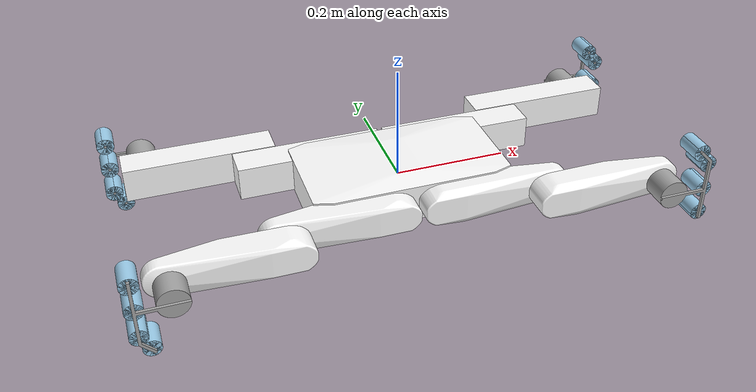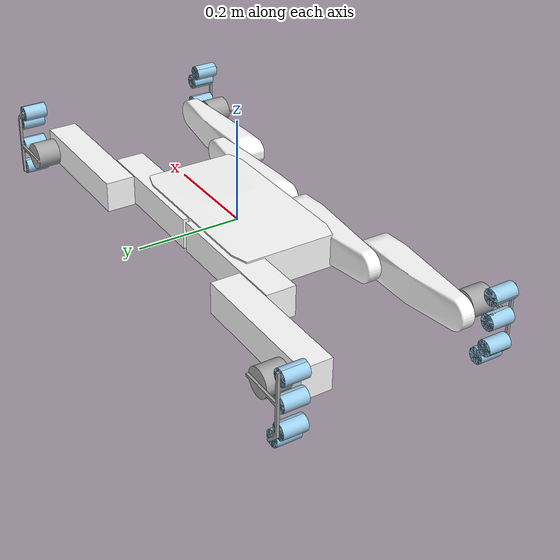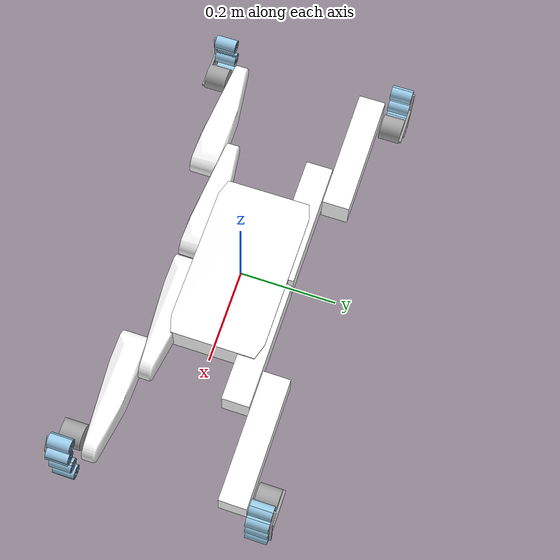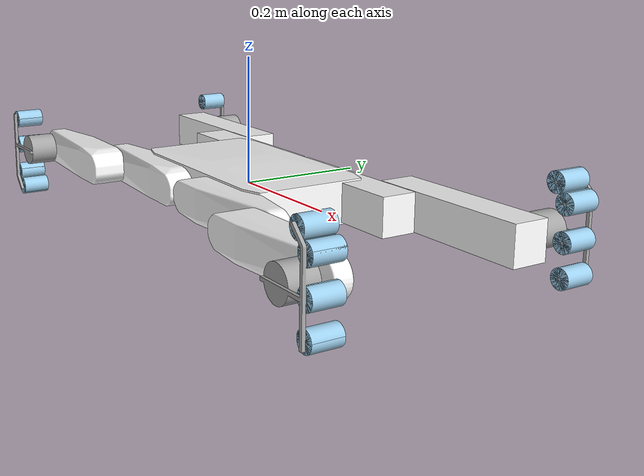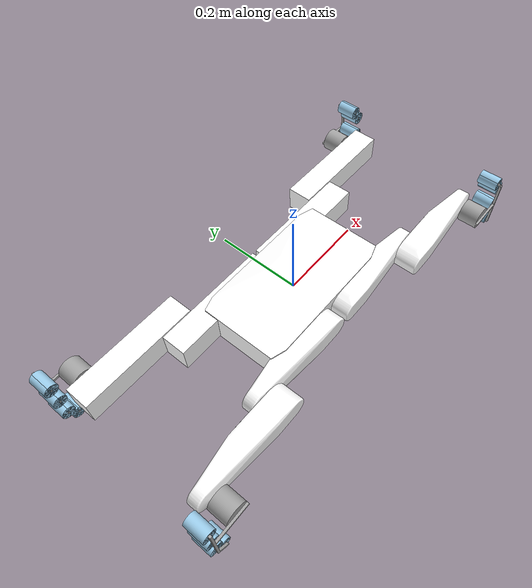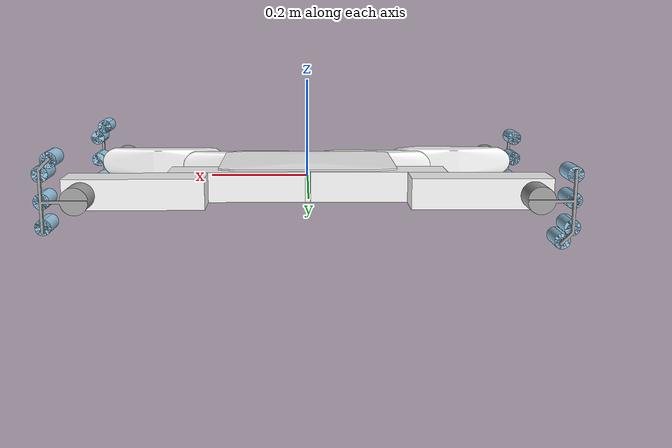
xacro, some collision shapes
<?xml version="1.0"?>

<robot name="traquad" xmlns:xacro="http://ros.org/wiki/xacro">
    <!-- Simplified leg: hip + upper leg only TODO add the tracks -->
    <xacro:macro name="leg" params="prefix gazebo jnt_pref simplify_meshes feet_type">
        <xacro:hip
            prefix="${prefix}"
            gazebo="${gazebo}"
            jnt_pref="${jnt_pref}"
            simplify_meshes="${simplify_meshes}"/>
        <xacro:upper_leg
            prefix="${prefix}"
            gazebo="${gazebo}"
            jnt_pref="${jnt_pref}"
            simplify_meshes="${simplify_meshes}"/>
    </xacro:macro>

    <!-- Vi consiglio di creare xacro con i track e lo includete qui -->
    <xacro:include filename="$(find mulinex_description)/urdf/links.xacro" />
    <xacro:include filename="$(find mulinex_description)/urdf/material.xacro" />
    <xacro:include filename="$(find mulinex_description)/urdf/traquad_hw_ign.xacro" />
    <xacro:include filename="$(find mulinex_description)/urdf/imu_sensor.xacro" />
    <xacro:include filename="$(find mulinex_description)/urdf/lidar_sensor.xacro" />

    <xacro:include filename="$(find mulinex_description)/urdf/track.xacro" />

    <xacro:property name="mulinex_base" value="file://$(find mulinex_description)/meshes//Body.stl" />
    <xacro:arg name="use_gazebo" default="true" />
    <xacro:arg name="mulinex_namespace" default="mulinex"/>
    <xacro:arg name="lidar_3D" default="true"/>
    <xacro:arg name="enable_lidar" default="false"/>
    <xacro:arg name="enable_imu" default="false"/>
    <xacro:arg name="yaml_file" default=""/>

    <xacro:arg name="simplify_meshes_lower_leg" default="true"/>

    <!-- use "normal" if normal feet are used
        use "omni" if omniwheels are used
        use "goat" if goat feet are used
        use "track" if track feet are used -->
    <xacro:arg name="feet_type" default="normal"/>

    <xacro:arg name="jnt_prefix" default="" />
    <xacro:arg name="front_haa" default="0.0" />
    <xacro:arg name="hind_haa" default="0.0" />

    <xacro:arg name="RH_HFE" default="0.0" />
    <xacro:arg name="RH_KFE" default="0.0" />
    <xacro:arg name="RF_HFE" default="0.0" />
    <xacro:arg name="RF_KFE" default="0.0" />

    <xacro:arg name="LH_HFE" default="0.0" />
    <xacro:arg name="LH_KFE" default="0.0" />
    <xacro:arg name="LF_HFE" default="0.0" />
    <xacro:arg name="LF_KFE" default="0.0" />

    <link name="$(arg jnt_prefix)base_link">
        <visual>
            <material name="white" />
            <origin xyz="0 0 0" rpy="0 0 0" />
            <geometry>
                <mesh filename="${mulinex_base}" />
            </geometry>
        </visual>
        <collision>
            <origin xyz="0 0 0" rpy="0 0 0" />
            <geometry>
                <box size="0.353 0.090 0.066" />
            </geometry>
        </collision>
        <inertial>
            <mass value="1.3008737" />
            <origin xyz="-1.4565496e-03 -2.5110071e-03 -4.2484136e-03" rpy="0 0 0" />
            <inertia ixx="4.0762590e-03" ixy="-2.5234809e-05" ixz="-3.2587794e-06"
                iyy="9.2413606e-03" iyz="-8.0660183e-06"
                izz="1.2268730e-02" />
        </inertial>
    </link>

    <gazebo>

        <plugin
            filename="ignition-gazebo-odometry-publisher-system"
            name="ignition::gazebo::systems::OdometryPublisher">
            <dimensions>3</dimensions>
            <odom_publish_frequency>30</odom_publish_frequency>
            <odom_frame>$(arg mulinex_namespace)/gt_odom</odom_frame>
            <robot_base_frame>$(arg mulinex_namespace)/base_link</robot_base_frame>
            <odom_topic>$(arg mulinex_namespace)/gt_odom</odom_topic>
            <tf_topic>$(arg mulinex_namespace)/gt_pose_gazebo</tf_topic>
        </plugin>
    </gazebo>

    <xacro:leg
        prefix="LH"
        gazebo="$(arg use_gazebo)"
        jnt_pref="$(arg jnt_prefix)"
        simplify_meshes="$(arg simplify_meshes_lower_leg)"
        feet_type="$(arg feet_type)"
        />
    <xacro:leg
        prefix="LF"
        gazebo="$(arg use_gazebo)"
        jnt_pref="$(arg jnt_prefix)"
        simplify_meshes="$(arg simplify_meshes_lower_leg)"
        feet_type="$(arg feet_type)"
        />
    <xacro:leg
        prefix="RF"
        gazebo="$(arg use_gazebo)"
        jnt_pref="$(arg jnt_prefix)"
        simplify_meshes="$(arg simplify_meshes_lower_leg)"
        feet_type="$(arg feet_type)"
        />
    <xacro:leg
        prefix="RH"
        gazebo="$(arg use_gazebo)"
        jnt_pref="$(arg jnt_prefix)"
        simplify_meshes="$(arg simplify_meshes_lower_leg)"
        feet_type="$(arg feet_type)"
        />
    <xacro:body_left  name="LH" parent="LH_UPPER_LEG" xyz="-0.19 0.05 0" rpy="1.5708 0 1.5708"/>
    <xacro:body_left  name="LF" parent="LF_UPPER_LEG" xyz="0.19 0.05 0" rpy="-1.5708 0 1.5708"/>
    <xacro:body_right name="RF" parent="RF_UPPER_LEG" xyz="0.19 -0.05 0" rpy="3.14159 0 1.5708"/>
    <xacro:body_right name="RH" parent="RH_UPPER_LEG" xyz="-0.19 -0.05 0" rpy="0 0 1.5708"/>

    <!-- Wheels for each body (4 per leg) -->
    <xacro:wheel name="wheel_1_LH" parent="LH" xyz="0 0.0484 -0.0584" rpy="-6.12323e-17 -1.5708 0"/>
    <xacro:wheel name="wheel_2_LH" parent="LH" xyz="0 1.07779e-16 -0.0584" rpy="-6.12323e-17 -1.5708 0"/>
    <xacro:wheel name="wheel_3_LH" parent="LH" xyz="0 -0.05103 -0.0584" rpy="-6.12323e-17 -1.5708 0"/>
    <xacro:wheel name="wheel_4_LH" parent="LH" xyz="0 -0.07668 -0.0417" rpy="-6.12323e-17 -1.5708 0"/>

    <xacro:wheel name="wheel_1_LF" parent="LF" xyz="0 0.0484 -0.0584" rpy="-6.12323e-17 -1.5708 0"/>
    <xacro:wheel name="wheel_2_LF" parent="LF" xyz="0 1.07779e-16 -0.0584" rpy="-6.12323e-17 -1.5708 0"/>
    <xacro:wheel name="wheel_3_LF" parent="LF" xyz="0 -0.05103 -0.0584" rpy="-6.12323e-17 -1.5708 0"/>
    <xacro:wheel name="wheel_4_LF" parent="LF" xyz="0 -0.07668 -0.0417" rpy="-6.12323e-17 -1.5708 0"/>

    <xacro:wheel name="wheel_1_RF" parent="RF" xyz="2.08167e-17 0.05838 0.04841" rpy="-1.5708 0.992087 -1.5708"/>
    <xacro:wheel name="wheel_2_RF" parent="RF" xyz="0 0.05838 1.10544e-16" rpy="-1.5708 0.967866 -1.5708"/>
    <xacro:wheel name="wheel_3_RF" parent="RF" xyz="-2.08167e-17 0.05838 -0.05103" rpy="-1.5708 0.967866 -1.5708"/>
    <xacro:wheel name="wheel_4_RF" parent="RF" xyz="-3.46945e-17 0.04174 -0.07668" rpy="-1.5708 0.992087 -1.5708"/>

    <xacro:wheel name="wheel_1_RH" parent="RH" xyz="2.08167e-17 0.05838 0.04841" rpy="-1.5708 0.992087 -1.5708"/>
    <xacro:wheel name="wheel_2_RH" parent="RH" xyz="0 0.05838 1.10544e-16" rpy="-1.5708 0.967866 -1.5708"/>
    <xacro:wheel name="wheel_3_RH" parent="RH" xyz="-2.08167e-17 0.05838 -0.05103" rpy="-1.5708 0.967866 -1.5708"/>
    <xacro:wheel name="wheel_4_RH" parent="RH" xyz="-3.46945e-17 0.04174 -0.07668" rpy="-1.5708 0.992087 -1.5708"/>

    <xacro:if value="$(arg enable_imu)">
        <xacro:imu_sensor namespace="$(arg mulinex_namespace)"/>
    </xacro:if>
    <xacro:if value="$(arg enable_lidar)">
        <xacro:lidar_sensor tredi="$(arg lidar_3D)" namespace="$(arg mulinex_namespace)"/>
    </xacro:if>

    <xacro:traquad_ign_hw gazebo="$(arg use_gazebo)" yaml="$(arg yaml_file)"/>
</robot>

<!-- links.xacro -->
<robot xmlns:xacro="http://ros.org/wiki/xacro">

    <xacro:property name="base_2_HAA_y" value="${81.0 * 0.001}" />
    <xacro:property name="base_2_HAA_x" value="${45.0 * 0.001}" />

    <xacro:property name="HAA_2_HFE_x" value="${190.0 * 0.001}" />
    <xacro:property name="HAA_2_HFE_y" value="${44.0 * 0.001}" />

    <xacro:property name="HFE_2_KFE_x" value="${190.0 * 0.001}" />
    <xacro:property name="HFE_2_KFE_y" value="${44.0 * 0.001}" />

    <xacro:property name="KFE_2_FOOT_x" value="${190.0 * 0.001}" />
    <xacro:property name="KFE_2_FOOT_y" value="${28.0 * 0.001}" />

    <xacro:property name="ANKLE_2_ROLL1_x" value="${70.0 * 0.001}" />
    <xacro:property name="ANKLE_2_ROLL1_y" value="${8.0 * 0.001}" />

    <xacro:property name="ANKLE_2_ROLL2_x" value="${44.0 * 0.001}" />
    <xacro:property name="ANKLE_2_ROLL2_y" value="${19.0 * 0.001}" />

    <xacro:property name="ANKLE_2_ROLL3_x" value="${33.0 * 0.001}" />
    <xacro:property name="ANKLE_2_ROLL3_y" value="${58.0 * 0.001}" />

    <xacro:property name="PI" value="3.141592" />

    <!-- MULINEX VISUALIZATION meshes -->

    <xacro:property name="mulinex_module_left_front"
        value="file://$(find mulinex_description)/meshes//Module_left_front.stl" />
    <xacro:property name="mulinex_module_left_hind"
        value="file://$(find mulinex_description)/meshes//Module_left_hind.stl" />
    <xacro:property name="mulinex_module_2_left"
        value="file://$(find mulinex_description)/meshes//Module_2_left.stl" />
    <xacro:property name="mulinex_lower_leg_left"
        value="file://$(find mulinex_description)/meshes//Lower_leg_left.stl" />
    <xacro:property name="mulinex_module_right_front"
        value="file://$(find mulinex_description)/meshes//Module_right_front.stl" />
    <xacro:property name="mulinex_module_right_hind"
        value="file://$(find mulinex_description)/meshes//Module_right_hind.stl" />
    <xacro:property name="mulinex_module_2_right"
        value="file://$(find mulinex_description)/meshes//Module_2_right.stl" />
    <xacro:property name="mulinex_lower_leg_right"
        value="file://$(find mulinex_description)/meshes//Lower_leg_right.stl" />

    <xacro:property name="old_mulinex_base"
        value="file://$(find mulinex_description)/meshes//old_Body.stl" />
    <xacro:property name="old_mulinex_module_left_front"
        value="file://$(find mulinex_description)/meshes//old_Module_left_front.stl" />
    <xacro:property name="old_mulinex_module_left_hind"
        value="file://$(find mulinex_description)/meshes//old_Module_left_hind.stl" />
    <xacro:property name="old_mulinex_module_2_left"
        value="file://$(find mulinex_description)/meshes//old_Module_2_left.stl" />
    <xacro:property name="old_mulinex_lower_leg_left"
        value="file://$(find mulinex_description)/meshes//old_Lower_leg_left.stl" />
    <xacro:property name="old_mulinex_module_right_front"
        value="file://$(find mulinex_description)/meshes//old_Module_right_front.stl" />
    <xacro:property name="old_mulinex_module_right_hind"
        value="file://$(find mulinex_description)/meshes//old_Module_right_hind.stl" />
    <xacro:property name="old_mulinex_module_2_right"
        value="file://$(find mulinex_description)/meshes//old_Module_2_right.stl" />
    <xacro:property name="old_mulinex_lower_leg_right"
        value="file://$(find mulinex_description)/meshes//old_Lower_leg_right.stl" />

    <!-- GOAT MESHES -->

    <xacro:property name="goat_lower_leg_LF"
        value="file://$(find mulinex_description)/meshes//goat_lower_leg_LF.STL" />
    <xacro:property name="goat_lower_leg_LH"
        value="file://$(find mulinex_description)/meshes//goat_lower_leg_LH.STL" />
    <xacro:property name="goat_lower_leg_RF"
        value="file://$(find mulinex_description)/meshes//goat_lower_leg_RF.STL" />
    <xacro:property name="goat_lower_leg_RH"
        value="file://$(find mulinex_description)/meshes//goat_lower_leg_RH.STL" />

    <xacro:property name="goat_upper_foot_LF"
        value="file://$(find mulinex_description)/meshes//goat_upper_foot_LF.STL" />
    <xacro:property name="goat_upper_foot_LH"
        value="file://$(find mulinex_description)/meshes//goat_upper_foot_LH.STL" />
    <xacro:property name="goat_upper_foot_RF"
        value="file://$(find mulinex_description)/meshes//goat_upper_foot_RF.STL" />
    <xacro:property name="goat_upper_foot_RH"
        value="file://$(find mulinex_description)/meshes//goat_upper_foot_RH.STL" />

    <xacro:property name="goat_lower_foot_LF"
        value="file://$(find mulinex_description)/meshes//goat_lower_foot_LF.STL" />
    <xacro:property name="goat_lower_foot_LH"
        value="file://$(find mulinex_description)/meshes//goat_lower_foot_LH.STL" />
    <xacro:property name="goat_lower_foot_RF"
        value="file://$(find mulinex_description)/meshes//goat_lower_foot_RF.STL" />
    <xacro:property name="goat_lower_foot_RH"
        value="file://$(find mulinex_description)/meshes//goat_lower_foot_RH.STL" />

    <!-- OMNI MESHES -->

    <xacro:property name="omni_lower_leg_LF"
        value="file://$(find mulinex_description)/meshes//omni_lower_leg_LF.STL" />
    <xacro:property name="omni_lower_leg_LH"
        value="file://$(find mulinex_description)/meshes//omni_lower_leg_LH.STL" />
    <xacro:property name="omni_lower_leg_RF"
        value="file://$(find mulinex_description)/meshes//omni_lower_leg_RF.STL" />
    <xacro:property name="omni_lower_leg_RH"
        value="file://$(find mulinex_description)/meshes//omni_lower_leg_RH.STL" />

    <xacro:property name="mulinex_roller"
        value="file://$(find mulinex_description)/meshes//roller_1.STL" />
    <xacro:property name="mulinex_mec_wheel_LF"
        value="file://$(find mulinex_description)/meshes//mecanum_wheel_lf.STL" />
    <xacro:property name="mulinex_mec_wheel_RF"
        value="file://$(find mulinex_description)/meshes//mecanum_wheel_rf.STL" />
    <xacro:property name="mulinex_mec_wheel_LH"
        value="file://$(find mulinex_description)/meshes//mecanum_wheel_lh.STL" />
    <xacro:property name="mulinex_mec_wheel_RH"
        value="file://$(find mulinex_description)/meshes//mecanum_wheel_rh.STL" />

    <!-- EACH MACRO CONSISTS OF THE LINK AND ITS PREVIOUS JOINT -->

    <!-- HIP -->
    <xacro:macro name="hip" params="prefix gazebo jnt_pref simplify_meshes">
        <!-- Transformation based on the position of each link -->
        <xacro:if value="${prefix == 'LF'}">
            <xacro:property name="base_to_hip_xyz" value="${base_2_HAA_x} ${base_2_HAA_y} 0" />
        </xacro:if>
        <xacro:if
            value="${prefix == 'LH'}">
            <xacro:property name="base_to_hip_xyz" value="${-base_2_HAA_x} ${base_2_HAA_y} 0" />
        </xacro:if>
        <xacro:if
            value="${prefix == 'RF'}">
            <xacro:property name="base_to_hip_xyz" value="${base_2_HAA_x} ${-base_2_HAA_y} 0" />
        </xacro:if>
        <xacro:if
            value="${prefix == 'RH'}">
            <xacro:property name="base_to_hip_xyz" value="${-base_2_HAA_x} ${-base_2_HAA_y} 0" />
        </xacro:if>

        <!-- Joint to fix the leg to the base -->
        <joint name="${prefix}_HAA" type="fixed">
            <parent link="${jnt_pref}base_link" />
            <child link="${jnt_pref}${prefix}_SHOULDER" />
            <origin xyz="${base_to_hip_xyz}" rpy="0 0 0" />
        </joint>
        <!-- Shoulder link -->
        <link name="${prefix}_SHOULDER">
            <visual>
                <material name="white" />
                <xacro:if value="${prefix == 'LF'}">
                    <origin xyz="0 0 0" rpy="0 0 0" />
                    <geometry>
                        <xacro:if value="${simplify_meshes}">
                            <mesh filename="${mulinex_module_left_front}" />
                        </xacro:if>
                        <xacro:unless value="${simplify_meshes}">
                            <mesh filename="${old_mulinex_module_left_front}" />
                        </xacro:unless>
                    </geometry>
                </xacro:if>
                <xacro:if value="${prefix == 'LH'}">
                    <origin xyz="0 0 0" rpy="0 0 0" />
                    <geometry>
                        <xacro:if value="${simplify_meshes}">
                            <mesh filename="${mulinex_module_left_hind}" />
                        </xacro:if>
                        <xacro:unless value="${simplify_meshes}">
                            <mesh filename="${old_mulinex_module_left_hind}" />
                        </xacro:unless>
                    </geometry>
                </xacro:if>
                <xacro:if value="${prefix == 'RF'}">
                    <origin xyz="0 0 0" rpy="0 0 0" />
                    <geometry>
                        <xacro:if value="${simplify_meshes}">
                            <mesh filename="${mulinex_module_right_front}" />
                        </xacro:if>
                        <xacro:unless value="${simplify_meshes}">
                            <mesh filename="${old_mulinex_module_right_front}" />
                        </xacro:unless>
                    </geometry>
                </xacro:if>
                <xacro:if value="${prefix == 'RH'}">
                    <origin xyz="0 0 0" rpy="0 0 0" />
                    <geometry>
                        <xacro:if value="${simplify_meshes}">
                            <mesh filename="${mulinex_module_right_hind}" />
                        </xacro:if>
                        <xacro:unless value="${simplify_meshes}">
                            <mesh filename="${old_mulinex_module_right_hind}" />
                        </xacro:unless>
                    </geometry>
                </xacro:if>
            </visual>

            <collision>
                <xacro:if value="${prefix == 'LF'}">
                    <origin xyz="0.0945 0 0" rpy="0 0 0" />
                    <geometry>
                        <box size="0.269 0.057 0.060" />
                    </geometry>
                </xacro:if>
                <xacro:if value="${prefix == 'LH'}">
                    <origin xyz="-0.0945 0 0" rpy="0 0 0" />
                    <geometry>
                        <box size="0.269 0.057 0.060" />
                    </geometry>
                </xacro:if>
                <xacro:if value="${prefix == 'RF'}">
                    <origin xyz="0.0945 0 0" rpy="0 0 0" />
                    <geometry>
                        <box size="0.269 0.057 0.060" />
                    </geometry>
                </xacro:if>
                <xacro:if value="${prefix == 'RH'}">
                    <origin xyz="-0.0945 0 0" rpy="0 0 0" />
                    <geometry>
                        <box size="0.269 0.057 0.060" />
                    </geometry>
                </xacro:if>
            </collision>

            <inertial>
                <mass value="0.47669673" />
                <xacro:if value="${prefix == 'LF'}">
                    <origin
                        xyz="7.2487360e-02 3.1582591e-02 -2.4812434e-03"
                        rpy="0 0 0" />
                    <inertia ixx="2.1574269e-04" ixy="-3.3437484e-05"
                        ixz="-2.4284668e-06" iyy="3.0607390e-03"
                        iyz="-2.0388977e-06" izz="3.0504273e-03" />
                </xacro:if>
                <xacro:if value="${prefix == 'LH'}">
                    <origin
                        xyz="-7.2487360e-02 3.1582591e-02 2.4812434e-03"
                        rpy="0 0 0" />
                    <inertia ixx="2.1574269e-04" ixy="3.3437484e-05"
                        ixz="-2.4284668e-06" iyy="3.0607390e-03"
                        iyz="-2.0388977e-06" izz="3.0504273e-03" />
                </xacro:if>
                <xacro:if value="${prefix == 'RF'}">
                    <origin
                        xyz="7.2487360e-02 -3.1582591e-02 2.4812434e-03"
                        rpy="0 0 0" />
                    <inertia ixx="2.1574269e-04" ixy="3.3437484e-05"
                        ixz="2.4284668e-06" iyy="3.0607390e-03"
                        iyz="-2.0388977e-06" izz="3.0504273e-03" />
                </xacro:if>
                <xacro:if value="${prefix == 'RH'}">
                    <origin
                        xyz="-7.2487360e-02 -3.1582591e-02 -2.4812434e-03"
                        rpy="0 0 0" />
                    <inertia ixx="2.1574269e-04" ixy="-3.3437484e-05"
                        ixz="2.4284668e-06" iyy="3.0607390e-03"
                        iyz="-2.0388977e-06" izz="3.0504273e-03" />
                </xacro:if>
            </inertial>
        </link>
        <xacro:if value="${gazebo}">
            <gazebo reference="${prefix}_SHOULDER">
                <material>Gazebo/White</material>
                <collision>
                    <surface>
                        <friction>
                            <ode>
                                <mu>1</mu>
                                <mu2>1</mu2>
                                <slip1>0</slip1>
                                <slip2>0</slip2>
                            </ode>
                        </friction>
                        <contact>
                            <ode>
                                <kp>1000000.0</kp>
                                <kd>100.0</kd>
                                <min_depth>0.001</min_depth>
                            </ode>
                        </contact>
                    </surface>
                </collision>
            </gazebo>
        </xacro:if>
    </xacro:macro>

    <!-- UPPER LEG -->
    <xacro:macro name="upper_leg" params="prefix gazebo jnt_pref simplify_meshes">
        <!-- Transformation based on the position of each link -->
        <xacro:if value="${prefix == 'LF'}">
            <xacro:property name="hip_to_upper_leg_xyz" value="${HAA_2_HFE_x} ${HAA_2_HFE_y} 0" />
            <xacro:property name="hip_to_upper_leg_rpy" value="0 0 0" />
            <xacro:property name="axis" value="0 1 0" />
        </xacro:if>
        <xacro:if
            value="${prefix == 'LH'}">
            <xacro:property name="hip_to_upper_leg_xyz" value="${-HAA_2_HFE_x} ${HAA_2_HFE_y} 0" />
            <xacro:property name="hip_to_upper_leg_rpy" value="0 0 0" />
            <xacro:property name="axis" value="0 1 0" />
        </xacro:if>
        <xacro:if
            value="${prefix == 'RF'}">
            <xacro:property name="hip_to_upper_leg_xyz" value="${HAA_2_HFE_x} ${-HAA_2_HFE_y} 0" />
            <xacro:property name="hip_to_upper_leg_rpy" value="0 0 0" />
            <xacro:property name="axis" value="0 -1 0" />
        </xacro:if>
        <xacro:if
            value="${prefix == 'RH'}">
            <xacro:property name="hip_to_upper_leg_xyz" value="${-HAA_2_HFE_x} ${-HAA_2_HFE_y} 0" />
            <xacro:property name="hip_to_upper_leg_rpy" value="0 0 0" />
            <xacro:property name="axis" value="0 -1 0" />
        </xacro:if>

        <!-- Hip joint -->
        <joint name="${prefix}_HFE" type="revolute">
            <parent link="${jnt_pref}${prefix}_SHOULDER" />
            <child link="${jnt_pref}${prefix}_UPPER_LEG" />
            <origin xyz="${hip_to_upper_leg_xyz}" rpy="${hip_to_upper_leg_rpy}" />
            <axis xyz="${axis}" />
            <limit effort="5.0" lower="-${2*PI}" upper="${2*PI}" velocity="1000" />
        </joint>
        <!-- Upper leg link -->
        <link name="${prefix}_UPPER_LEG">
            <visual>
                <material name="white" />
                <xacro:if value="${prefix == 'LF'}">
                    <origin xyz="0 0 0" rpy="0 0 0" />
                    <geometry>
                        <xacro:if value="${simplify_meshes}">
                            <mesh filename="${mulinex_module_left_front}" />
                        </xacro:if>
                        <xacro:unless value="${simplify_meshes}">
                            <mesh filename="${old_mulinex_module_left_front}" />
                        </xacro:unless>
                    </geometry>
                </xacro:if>

                <xacro:if value="${prefix == 'LH'}">
                    <origin xyz="0 0 0" rpy="0 0 0" />
                    <geometry>
                        <xacro:if value="${simplify_meshes}">
                            <mesh filename="${mulinex_module_left_hind}" />
                        </xacro:if>
                        <xacro:unless value="${simplify_meshes}">
                            <mesh filename="${old_mulinex_module_left_hind}" />
                        </xacro:unless>
                    </geometry>
                </xacro:if>

                <xacro:if value="${prefix == 'RF'}">
                    <origin xyz="0 0 0" rpy="0 0 0" />
                    <geometry>
                        <xacro:if value="${simplify_meshes}">
                            <mesh filename="${mulinex_module_right_front}" />
                        </xacro:if>
                        <xacro:unless value="${simplify_meshes}">
                            <mesh filename="${old_mulinex_module_right_front}" />
                        </xacro:unless>
                    </geometry>
                </xacro:if>

                <xacro:if value="${prefix == 'RH'}">
                    <origin xyz="0 0 0" rpy="0 0 0" />
                    <geometry>
                        <xacro:if value="${simplify_meshes}">
                            <mesh filename="${mulinex_module_right_hind}" />
                        </xacro:if>
                        <xacro:unless value="${simplify_meshes}">
                            <mesh filename="${old_mulinex_module_right_hind}" />
                        </xacro:unless>
                    </geometry>
                </xacro:if>
            </visual>

            <collision>
                <xacro:if value="${prefix == 'LF'}">
                    <origin xyz="0.0945 0.015 0" rpy="0 0 0" />
                    <geometry>
                        <box size="0.269 0.057 0.060" />
                    </geometry>
                </xacro:if>
                <xacro:if value="${prefix == 'LH'}">
                    <origin xyz="-0.0945 0.015 0" rpy="0 0 0" />
                    <geometry>
                        <box size="0.269 0.057 0.060" />
                    </geometry>
                </xacro:if>
                <xacro:if value="${prefix == 'RF'}">
                    <origin xyz="0.0945 -0.015 0" rpy="0 0 0" />
                    <geometry>
                        <box size="0.269 0.057 0.060" />
                    </geometry>
                </xacro:if>
                <xacro:if value="${prefix == 'RH'}">
                    <origin xyz="-0.0945 -0.015 0" rpy="0 0 0" />
                    <geometry>
                        <box size="0.269 0.057 0.060" />
                    </geometry>
                </xacro:if>

            </collision>

            <inertial>
                <mass value="0.47669673" />
                <xacro:if value="${prefix == 'LF'}">
                    <origin
                        xyz="7.2487360e-02 3.1582591e-02 -2.4812434e-03"
                        rpy="0 0 0" />
                    <inertia ixx="2.1574269e-04" ixy="-3.3437484e-05"
                        ixz="-2.4284668e-06" iyy="3.0607390e-03"
                        iyz="-2.0388977e-06" izz="3.0504273e-03" />
                </xacro:if>
                <xacro:if value="${prefix == 'LH'}">
                    <origin
                        xyz="-7.2487360e-02 3.1582591e-02 2.4812434e-03"
                        rpy="0 0 0" />
                    <inertia ixx="2.1574269e-04" ixy="3.3437484e-05"
                        ixz="-2.4284668e-06" iyy="3.0607390e-03"
                        iyz="-2.0388977e-06" izz="3.0504273e-03" />
                </xacro:if>
                <xacro:if value="${prefix == 'RF'}">
                    <origin
                        xyz="7.2487360e-02 -3.1582591e-02 2.4812434e-03"
                        rpy="0 0 0" />
                    <inertia ixx="2.1574269e-04" ixy="3.3437484e-05"
                        ixz="2.4284668e-06" iyy="3.0607390e-03"
                        iyz="-2.0388977e-06" izz="3.0504273e-03" />
                </xacro:if>
                <xacro:if value="${prefix == 'RH'}">
                    <origin
                        xyz="-7.2487360e-02 -3.1582591e-02 -2.4812434e-03"
                        rpy="0 0 0" />
                    <inertia ixx="2.1574269e-04" ixy="-3.3437484e-05"
                        ixz="2.4284668e-06" iyy="3.0607390e-03"
                        iyz="-2.0388977e-06" izz="3.0504273e-03" />
                </xacro:if>
            </inertial>
        </link>
        <xacro:if value="${gazebo}">
            <gazebo reference="${prefix}_UPPER_LEG">
                <material>Gazebo/White</material>
                <collision>
                    <surface>
                        <friction>
                            <ode>
                                <mu>1</mu>
                                <mu2>1</mu2>
                                <slip1>0</slip1>
                                <slip2>0</slip2>
                            </ode>
                        </friction>
                        <contact>
                            <ode>
                                <kp>1000000.0</kp>
                                <kd>100.0</kd>
                                <min_depth>0.001</min_depth>
                            </ode>
                        </contact>
                    </surface>
                </collision>
            </gazebo>
        </xacro:if>
    </xacro:macro>

    <!-- LOWER LEG -->
    <xacro:macro name="lower_leg" params="prefix gazebo jnt_pref simplify_meshes feet_type">
        <!-- NORMAL FEET CONFIGURATION -->
        <xacro:if value="${feet_type == 'normal'}">
            <!-- Transformation based on the position of each link -->
            <xacro:if value="${prefix == 'LF'}">
                <xacro:property name="upper_to_lower_leg_xyz"
                    value="${HFE_2_KFE_x} ${HFE_2_KFE_y} 0" />
                <xacro:property name="axis" value="0 1 0" />
            </xacro:if>
            <xacro:if
                value="${prefix == 'LH'}">
                <xacro:property name="upper_to_lower_leg_xyz"
                    value="${-HFE_2_KFE_x} ${HFE_2_KFE_y} 0" />
                <xacro:property name="axis" value="0 1 0" />
            </xacro:if>
            <xacro:if
                value="${prefix == 'RF'}">
                <xacro:property name="upper_to_lower_leg_xyz"
                    value="${HFE_2_KFE_x} ${-HFE_2_KFE_y} 0" />
                <xacro:property name="axis" value="0 -1 0" />
            </xacro:if>
            <xacro:if
                value="${prefix == 'RH'}">
                <xacro:property name="upper_to_lower_leg_xyz"
                    value="${-HFE_2_KFE_x} ${-HFE_2_KFE_y} 0" />
                <xacro:property name="axis" value="0 -1 0" />
            </xacro:if>

            <xacro:property name="upper_to_lower_leg_rpy" value="0 0 0" />

            <!-- Knee joint -->
            <joint name="${prefix}_KFE" type="revolute">
                <parent link="${jnt_pref}${prefix}_UPPER_LEG" />
                <child link="${jnt_pref}${prefix}_LOWER_LEG" />
                <origin xyz="${upper_to_lower_leg_xyz}" rpy="${upper_to_lower_leg_rpy}" />
                <axis xyz="${axis}" />
                <limit effort="5.0" lower="-${2*PI}" upper="${2*PI}" velocity="1000" />
            </joint>
            <!-- Lower leg link -->
            <link name="${prefix}_LOWER_LEG">
                <visual>
                    <material name="white" />
                    <xacro:if value="${prefix == 'LF'}">
                        <origin xyz="0 0 0" rpy="0 ${-PI/2} 0" />
                        <geometry>
                            <xacro:if value="${simplify_meshes}">
                                <mesh filename="${mulinex_lower_leg_left}" />
                            </xacro:if>
                            <xacro:unless value="${simplify_meshes}">
                                <mesh filename="${old_mulinex_lower_leg_left}" />
                            </xacro:unless>
                        </geometry>
                    </xacro:if>
                    <xacro:if value="${prefix == 'LH'}">
                        <origin xyz="0 0 0" rpy="0 ${PI/2} 0" />
                        <geometry>
                            <xacro:if value="${simplify_meshes}">
                                <mesh filename="${mulinex_lower_leg_left}" />
                            </xacro:if>
                            <xacro:unless value="${simplify_meshes}">
                                <mesh filename="${old_mulinex_lower_leg_left}" />
                            </xacro:unless>
                        </geometry>
                    </xacro:if>
                    <xacro:if value="${prefix == 'RF'}">
                        <origin xyz="0 0 0" rpy="0 ${-PI/2} 0" />
                        <geometry>
                            <xacro:if value="${simplify_meshes}">
                                <mesh filename="${mulinex_lower_leg_right}" />
                            </xacro:if>
                            <xacro:unless value="${simplify_meshes}">
                                <mesh filename="${old_mulinex_lower_leg_right}" />
                            </xacro:unless>
                        </geometry>
                    </xacro:if>
                    <xacro:if value="${prefix == 'RH'}">
                        <origin xyz="0 0 0" rpy="0 ${PI/2} 0" />
                        <geometry>
                            <xacro:if value="${simplify_meshes}">
                                <mesh filename="${mulinex_lower_leg_right}" />
                            </xacro:if>
                            <xacro:unless value="${simplify_meshes}">
                                <mesh filename="${old_mulinex_lower_leg_right}" />
                            </xacro:unless>
                        </geometry>
                    </xacro:if>
                </visual>
                <collision name="${prefix}_LOWER_LEG">
                    <!-- Real meshes -->
                    <xacro:unless value="${simplify_meshes}">
                        <xacro:if value="${prefix == 'LF'}">
                            <origin xyz="0 0 0" rpy="0 ${-PI/2} 0" />
                            <geometry>
                                <mesh filename="${mulinex_lower_leg_left}" />
                            </geometry>
                        </xacro:if>
                        <xacro:if value="${prefix == 'LH'}">
                            <origin xyz="0 0 0" rpy="0 ${PI/2} 0" />
                            <geometry>
                                <mesh filename="${mulinex_lower_leg_left}" />
                            </geometry>
                        </xacro:if>
                        <xacro:if value="${prefix == 'RF'}">
                            <origin xyz="0 0 0" rpy="0 ${-PI/2} 0" />
                            <geometry>
                                <mesh filename="${mulinex_lower_leg_right}" />
                            </geometry>
                        </xacro:if>
                        <xacro:if value="${prefix == 'RH'}">
                            <origin xyz="0 0 0" rpy="0 ${PI/2} 0" />
                            <geometry>
                                <mesh filename="${mulinex_lower_leg_right}" />
                            </geometry>
                        </xacro:if>
                    </xacro:unless>
                    <!-- Simplified meshes -->
                    <xacro:if value="${simplify_meshes}">
                        <xacro:if value="${prefix == 'LF'}">
                            <origin xyz="0.096 0.012 0.0" rpy="0 ${-PI/2} 0" />
                            <geometry>
                                <box size="0.032 0.024 0.192" />
                            </geometry>
                        </xacro:if>
                        <xacro:if value="${prefix == 'LH'}">
                            <origin xyz="-0.096 0.012 0.0" rpy="0 ${PI/2} 0" />
                            <geometry>
                                <box size="0.032 0.024 0.192" />
                            </geometry>
                        </xacro:if>
                        <xacro:if value="${prefix == 'RF'}">
                            <origin xyz="0.096 -0.012 0.0" rpy="0 ${-PI/2} 0" />
                            <geometry>
                                <box size="0.032 0.024 0.192" />
                            </geometry>
                        </xacro:if>
                        <xacro:if value="${prefix == 'RH'}">
                            <origin xyz="-0.096 -0.012 0.0" rpy="0 ${PI/2} 0" />
                            <geometry>
                                <box size="0.032 0.024 0.192" />
                            </geometry>
                        </xacro:if>
                    </xacro:if>
                </collision>
                <inertial>
                    <mass value="0.046942" />
                    <xacro:if value="${prefix == 'LF'}">
                        <origin
                            xyz="0.0660893 0.0198901 -1.552593e-05"
                            rpy="0 0 0" />
                        <inertia ixx="5.140780e-06" ixy="1.089102e-05"
                            ixz="2.468115e-08" iyy="0.00021242"
                            iyz="2.702972e-09" izz="0.00021154" />
                    </xacro:if>
                    <xacro:if value="${prefix == 'LH'}">
                        <origin
                            xyz="-0.0660893 0.0198901 1.552593e-05"
                            rpy="0 0 0" />
                        <inertia ixx="5.140780e-06" ixy="-1.089102e-05"
                            ixz="2.46811e-08" iyy="0.0002124295"
                            iyz="-2.702972e-09" izz="0.0002115478" />
                    </xacro:if>
                    <xacro:if value="${prefix == 'RF'}">
                        <origin
                            xyz="0.0660893 -0.0198901 -1.552593e-05"
                            rpy="0 0 0" />
                        <inertia ixx="5.140780e-06" ixy="1.089102e-05"
                            ixz="-2.468115e-08" iyy="0.00021242"
                            iyz="-2.702972e-09" izz="0.00021154" />
                    </xacro:if>
                    <xacro:if value="${prefix == 'RH'}">
                        <origin
                            xyz="-0.0660893 -0.0198901 1.552593e-05"
                            rpy="0 0 0" />
                        <inertia ixx="5.140780e-06" ixy="-1.089102e-05"
                            ixz="-2.46811e-08" iyy="0.0002124295"
                            iyz="2.702972e-09" izz="0.0002115478" />
                    </xacro:if>
                </inertial>
            </link>
            <xacro:if value="${gazebo}">
                <gazebo reference="${prefix}_LOWER_LEG">
                    <material>Gazebo/White</material>
                    <collision>
                        <surface>
                            <friction>
                                <ode>
                                    <mu>0.6</mu>
                                    <mu2>0.6</mu2>
                                    <slip1>0</slip1>
                                    <slip2>0</slip2>
                                </ode>
                            </friction>
                            <contact>
                                <ode>
                                    <kp>10000.0</kp>
                                    <kd>100.0</kd>
                                    <min_depth>0.001</min_depth>
                                </ode>
                            </contact>
                        </surface>
                    </collision>
                </gazebo>
            </xacro:if>

            <!-- Normal feet -->
            <joint name="${prefix}_ANKLE" type="fixed">
                <parent link="${prefix}_LOWER_LEG" />
                <child link="${prefix}_FOOT" />

                <xacro:if value="${prefix == 'LF'}">
                    <origin xyz="${KFE_2_FOOT_x} ${KFE_2_FOOT_y} 0" rpy="0 0 0" />
                </xacro:if>
                <xacro:if value="${prefix == 'LH'}">
                    <origin xyz="${-KFE_2_FOOT_x} ${KFE_2_FOOT_y} 0" rpy="0 0 0" />
                </xacro:if>
                <xacro:if value="${prefix == 'RF'}">
                    <origin xyz="${KFE_2_FOOT_x} ${-KFE_2_FOOT_y} 0" rpy="0 0 0" />
                </xacro:if>
                <xacro:if value="${prefix == 'RH'}">
                    <origin xyz="${-KFE_2_FOOT_x} ${-KFE_2_FOOT_y} 0" rpy="0 0 0" />
                </xacro:if>
            </joint>

            <!-- FOOT LINK -->
            <link name="${prefix}_FOOT">
                <xacro:if value="${simplify_meshes}">
                    <collision>
                        <origin xyz="0 0 0" rpy="0 0 0" />
                        <geometry>
                            <sphere radius="0.015" />
                        </geometry>
                    </collision>
                </xacro:if>
            </link>
            <xacro:if value="${gazebo}">
                <gazebo reference="${prefix}_FOOT">
                    <material>Gazebo/White</material>
                    <collision>
                        <surface>
                            <friction>
                                <ode>
                                    <mu>0.6</mu>
                                    <mu2>0.6</mu2>
                                    <slip1>0</slip1>
                                    <slip2>0</slip2>
                                </ode>
                            </friction>
                            <contact>
                                <ode>
                                    <kp>10000.0</kp>
                                    <kd>100.0</kd>
                                    <min_depth>0.001</min_depth>
                                </ode>
                            </contact>
                        </surface>
                    </collision>
                </gazebo>
            </xacro:if>
        </xacro:if>
        <!-- OMNIWHEELS CONFIGURATION -->
        <xacro:if value="${feet_type == 'omni'}">
            <!-- Transformation based on the position of each link -->
            <xacro:if value="${prefix == 'LF'}">
                <xacro:property name="upper_to_lower_leg_xyz"
                    value="${HFE_2_KFE_x} ${HFE_2_KFE_y} 0" />
                <xacro:property name="axis" value="0 1 0" />
            </xacro:if>
            <xacro:if
                value="${prefix == 'LH'}">
                <xacro:property name="upper_to_lower_leg_xyz"
                    value="${-HFE_2_KFE_x} ${HFE_2_KFE_y} 0" />
                <xacro:property name="axis" value="0 1 0" />
            </xacro:if>
            <xacro:if
                value="${prefix == 'RF'}">
                <xacro:property name="upper_to_lower_leg_xyz"
                    value="${HFE_2_KFE_x} ${-HFE_2_KFE_y} 0" />
                <xacro:property name="axis" value="0 -1 0" />
            </xacro:if>
            <xacro:if
                value="${prefix == 'RH'}">
                <xacro:property name="upper_to_lower_leg_xyz"
                    value="${-HFE_2_KFE_x} ${-HFE_2_KFE_y} 0" />
                <xacro:property name="axis" value="0 -1 0" />
            </xacro:if>

            <xacro:property name="upper_to_lower_leg_rpy" value="0 0 0" />

            <!-- Knee joint -->
            <joint name="${prefix}_KFE" type="revolute">
                <parent link="${jnt_pref}${prefix}_UPPER_LEG" />
                <child link="${jnt_pref}${prefix}_LOWER_LEG" />
                <origin xyz="${upper_to_lower_leg_xyz}" rpy="${upper_to_lower_leg_rpy}" />
                <axis xyz="${axis}" />
                <limit effort="5.0" lower="-${2*PI}" upper="${2*PI}" velocity="1000" />
            </joint>
            <!-- Lower leg link -->
            <link name="${prefix}_LOWER_LEG">
                <visual>
                    <material name="white" />
                    <xacro:if value="${prefix == 'LF'}">
                        <origin xyz="0 0 0" rpy="0 ${-PI/2} 0" />
                        <geometry>
                            <mesh filename="${mulinex_lower_leg_left}" />
                        </geometry>
                    </xacro:if>
                    <xacro:if value="${prefix == 'LH'}">
                        <origin xyz="0 0 0" rpy="0 ${PI/2} 0" />
                        <geometry>
                            <mesh filename="${mulinex_lower_leg_left}" />
                        </geometry>
                    </xacro:if>
                    <xacro:if value="${prefix == 'RF'}">
                        <origin xyz="0 0 0" rpy="0 ${-PI/2} 0" />
                        <geometry>
                            <mesh filename="${mulinex_lower_leg_right}" />
                        </geometry>
                    </xacro:if>
                    <xacro:if value="${prefix == 'RH'}">
                        <origin xyz="0 0 0" rpy="0 ${PI/2} 0" />
                        <geometry>
                            <mesh filename="${mulinex_lower_leg_right}" />
                        </geometry>
                    </xacro:if>
                </visual>
                <collision name="${prefix}_LOWER_LEG">
                    <!-- Real meshes -->
                    <xacro:unless value="${simplify_meshes}">
                        <xacro:if value="${prefix == 'LF'}">
                            <origin xyz="0 0 0" rpy="0 ${-PI/2} 0" />
                            <geometry>
                                <mesh filename="${mulinex_lower_leg_left}" />
                            </geometry>
                        </xacro:if>
                        <xacro:if value="${prefix == 'LH'}">
                            <origin xyz="0 0 0" rpy="0 ${PI/2} 0" />
                            <geometry>
                                <mesh filename="${mulinex_lower_leg_left}" />
                            </geometry>
                        </xacro:if>
                        <xacro:if value="${prefix == 'RF'}">
                            <origin xyz="0 0 0" rpy="0 ${-PI/2} 0" />
                            <geometry>
                                <mesh filename="${msphereulinex_lower_leg_right}" />
                            </geometry>
                        </xacro:if>
                        <xacro:if value="${prefix == 'RH'}">
                            <origin xyz="0 0 0" rpy="0 ${PI/2} 0" />
                            <geometry>
                                <mesh filename="${mulinex_lower_leg_right}" />
                            </geometry>
                        </xacro:if>
                    </xacro:unless>
                    <!-- Simplified meshes -->
                    <xacro:if value="${simplify_meshes}">
                        <xacro:if value="${prefix == 'LF'}">
                            <origin xyz="0.096 0.012 0.0" rpy="0 ${-PI/2} 0" />
                            <geometry>
                                <box size="0.032 0.024 0.192" />
                            </geometry>
                        </xacro:if>
                        <xacro:if value="${prefix == 'LH'}">
                            <origin xyz="-0.096 0.012 0.0" rpy="0 ${PI/2} 0" />
                            <geometry>
                                <box size="0.032 0.024 0.192" />
                            </geometry>
                        </xacro:if>
                        <xacro:if value="${prefix == 'RF'}">
                            <origin xyz="0.096 -0.012 0.0" rpy="0 ${-PI/2} 0" />
                            <geometry>
                                <box size="0.032 0.024 0.192" />
                            </geometry>
                        </xacro:if>
                        <xacro:if value="${prefix == 'RH'}">
                            <origin xyz="-0.096 -0.012 0.0" rpy="0 ${PI/2} 0" />
                            <geometry>
                                <box size="0.032 0.024 0.192" />
                            </geometry>
                        </xacro:if>
                    </xacro:if>
                </collision>
                <inertial>
                    <mass value="0.30551" />
                    <xacro:if value="${prefix == 'LF'}">
                        <origin
                            xyz="0.17801 0.030272 1.8448E-05"
                            rpy="0 0 0" />
                        <inertia
                            ixx="6.1505E-05"
                            ixy="-1.5369E-05"
                            ixz="-4.7734E-08"
                            iyy="0.00054256"
                            iyz="-1.9337E-08"
                            izz="0.00051876" />
                    </xacro:if>
                    <xacro:if value="${prefix == 'LH'}">
                        <origin
                            xyz="-0.17801 0.030272 -1.8448E-05"
                            rpy="0 0 0" />
                        <inertia
                            ixx="6.1505E-05"
                            ixy="1.5369E-05"
                            ixz="-4.7734E-08"
                            iyy="0.00054256"
                            iyz="1.9337E-08"
                            izz="0.00051876" />
                    </xacro:if>
                    <xacro:if value="${prefix == 'RF'}">
                        <origin
                            xyz="0.17801 -0.030272 -1.8448E-05"
                            rpy="0 0 0" />
                        <inertia
                            ixx="6.1505E-05"
                            ixy="1.5369E-05"
                            ixz="4.7734E-08"
                            iyy="0.00054256"
                            iyz="-1.9337E-08"
                            izz="0.00051876" />
                    </xacro:if>
                    <xacro:if value="${prefix == 'RH'}">
                        <origin
                            xyz="-0.17801 -0.030272 1.8448E-05"
                            rpy="0 0 0" />
                        <inertia
                            ixx="6.1505E-05"
                            ixy="-1.5369E-05"
                            ixz="4.7734E-08"
                            iyy="0.00054256"
                            iyz="1.9337E-08"
                            izz="0.00051876" />
                    </xacro:if>
                </inertial>
            </link>
            <xacro:if value="${gazebo}">
                <gazebo reference="${prefix}_LOWER_LEG">
                    <material>Gazebo/White</material>
                    <collision>
                        <surface>
                            <friction>
                                <ode>
                                    <mu>0.6</mu>
                                    <mu2>0.6</mu2>
                                    <slip1>0</slip1>
                                    <slip2>0</slip2>
                                </ode>
                            </friction>
                            <contact>
                                <ode>
                                    <kp>10000.0</kp>
                                    <kd>100.0</kd>
                                    <min_depth>0.001</min_depth>
                                </ode>
                            </contact>
                        </surface>
                    </collision>
                </gazebo>
            </xacro:if>

            <!-- Omniwheels -->
            <joint name="${prefix}_WHEEL_JNT" type="continuous">
                <parent link="${prefix}_LOWER_LEG" />
                <child link="${prefix}_WHEEL" />
                <xacro:if value="${prefix == 'LF'}">
                    <origin xyz="${KFE_2_FOOT_x} 0.01145 0" rpy="0 0 0" />
                    <axis xyz="0 1 0" />
                </xacro:if>
                <xacro:if value="${prefix == 'LH'}">
                    <origin xyz="${-KFE_2_FOOT_x} 0.01145 0" rpy="0 0 0" />
                    <axis xyz="0 1 0" />
                </xacro:if>
                <xacro:if value="${prefix == 'RF'}">
                    <origin xyz="${KFE_2_FOOT_x} -0.01145 0" rpy="0 0 0" />
                    <axis xyz="0 1 0" />
                </xacro:if>
                <xacro:if value="${prefix == 'RH'}">
                    <origin xyz="${-KFE_2_FOOT_x} -0.01145 0" rpy="0 0 0" />
                    <axis xyz="0 1 0" />
                </xacro:if>
            </joint>

            <link name="${prefix}_WHEEL">
                <visual>
                    <material name="white" />
                    <xacro:if value="${prefix == 'LF'}">
                        <origin xyz="0 0 0" rpy="0 0 0" />
                        <geometry>
                            <mesh filename="${mulinex_mec_wheel_LF}" />
                        </geometry>
                    </xacro:if>
                    <xacro:if value="${prefix == 'LH'}">
                        <origin xyz="0 0  0" rpy="0 0 0" />
                        <geometry>
                            <mesh filename="${mulinex_mec_wheel_LH}" />
                        </geometry>
                    </xacro:if>
                    <xacro:if value="${prefix == 'RF'}">
                        <origin xyz="0 0 0" rpy="0 0 0" />
                        <geometry>
                            <mesh filename="${mulinex_mec_wheel_RF}" />
                        </geometry>
                    </xacro:if>
                    <xacro:if value="${prefix == 'RH'}">
                        <origin xyz="0 0 0" rpy="0 0 0" />
                        <geometry>
                            <mesh filename="${mulinex_mec_wheel_RH}" />
                        </geometry>
                    </xacro:if>
                </visual>
                <!-- NO COLLISION FOR THE MECHANUM WHEELS -->
                <inertial>
                    <xacro:if value="${prefix == 'LF'}">
                        <origin xyz="0 0.047255 -2.335E-07" rpy="0 0 0" />
                        <mass value="0.078919" />
                        <inertia ixx="4.9627E-05" ixy="1.7873E-11"
                            ixz="-2.2576E-09" iyy="7.8948E-05"
                            iyz="-7.6317E-12" izz="4.9622E-05" />
                    </xacro:if>
                    <xacro:if value="${prefix == 'LH'}">
                        <origin xyz="0 0.047255 -1.5525E-07" rpy="0 0 0" />
                        <mass value="0.078525" />
                        <inertia ixx="4.9627E-05" ixy="-2.1009E-12"
                            ixz="-1.8882E-09" iyy="7.8948E-05"
                            iyz="4.4431E-12" izz="4.9622E-05" />
                    </xacro:if>
                    <xacro:if value="${prefix == 'RF'}">
                        <origin xyz="0 -0.047255 -1.5525E-07" rpy="0 0 0" />
                        <mass value="0.078525" />
                        <inertia ixx="4.9627E-05" ixy="-2.1009E-12"
                            ixz="1.8882E-09" iyy="7.8948E-05"
                            iyz="-4.4431E-12" izz="4.9622E-05" />
                    </xacro:if>
                    <xacro:if value="${prefix == 'RH'}">
                        <origin xyz="0 -0.047255 -2.3351E-07" rpy="0 0 0" />
                        <mass value="0.078919" />
                        <inertia ixx="4.9627E-05" ixy="1.7873E-11"
                            ixz="-2.2576E-09" iyy="7.8948E-05"
                            iyz="-7.6317E-12" izz="4.9622E-05" />
                    </xacro:if>
                </inertial>
            </link>
            <xacro:if value="${gazebo}">
                <gazebo reference="${prefix}_WHEEL">
                    <material>Gazebo/White</material>
                    <collision>
                        <surface>
                            <friction>
                                <ode>
                                    <mu>0.6</mu>
                                    <mu2>0.6</mu2>
                                    <slip1>0</slip1>
                                    <slip2>0</slip2>
                                </ode>
                            </friction>
                            <contact>
                                <ode>
                                    <kp>10000.0</kp>
                                    <kd>100.0</kd>
                                    <min_depth>0.001</min_depth>
                                </ode>
                            </contact>
                        </surface>
                    </collision>
                </gazebo>
            </xacro:if>

            <link name="${prefix}_Roller1">
                <xacro:if value="${prefix == 'LF'}">
                    <inertial>
                        <origin
                            xyz="0 0 6.3075E-15"
                            rpy="0 0 0" />
                        <mass
                            value="0.0059616" />
                        <inertia
                            ixx="7.911E-07"
                            ixy="1.2914E-12"
                            ixz="1.2242E-22"
                            iyy="7.9113E-07"
                            iyz="-5.294E-23"
                            izz="2.3532E-07" />
                    </inertial>
                    <visual>
                        <origin
                            xyz="0 0 0"
                            rpy="0 0 0" />
                        <geometry>
                            <mesh filename="${mulinex_roller}" />
                        </geometry>
                        <material
                            name="">
                            <color
                                rgba="0.29804 0.29804 0.29804 1" />
                        </material>
                    </visual>
                    <collision>
                        <origin
                            xyz="0 0 0"
                            rpy="0 0 0" />
                        <geometry>
                            <mesh filename="${mulinex_roller}" />
                        </geometry>
                    </collision>
                </xacro:if>
                <xacro:if value="${prefix == 'RF'}">
                    <inertial>
                        <origin
                            xyz="0 0 0"
                            rpy="0 0 0" />
                        <mass
                            value="0.0059616" />
                        <inertia
                            ixx="7.911E-07"
                            ixy="1.2914E-12"
                            ixz="2.5808E-22"
                            iyy="7.9113E-07"
                            iyz="-5.4263E-22"
                            izz="2.3532E-07" />
                    </inertial>
                    <visual>
                        <origin
                            xyz="0 0 0"
                            rpy="0 0 0" />
                        <geometry>
                            <mesh filename="${mulinex_roller}" />
                        </geometry>
                        <material
                            name="">
                            <color
                                rgba="0.29804 0.29804 0.29804 1" />
                        </material>
                    </visual>
                    <collision>
                        <origin
                            xyz="0 0 0"
                            rpy="0 0 0" />
                        <geometry>
                            <mesh filename="${mulinex_roller}" />
                        </geometry>
                    </collision>
                </xacro:if>
                <xacro:if value="${prefix == 'LH'}">
                    <inertial>
                        <origin
                            xyz="0 0 6.3075E-15"
                            rpy="0 0 0" />
                        <mass
                            value="0.0059616" />
                        <inertia
                            ixx="7.911E-07"
                            ixy="1.2914E-12"
                            ixz="1.9521E-22"
                            iyy="7.9113E-07"
                            iyz="-5.0954E-22"
                            izz="2.3532E-07" />
                    </inertial>
                    <visual>
                        <origin
                            xyz="0 0 0"
                            rpy="0 0 0" />
                        <geometry>
                            <mesh filename="${mulinex_roller}" />
                        </geometry>
                        <material
                            name="">
                            <color
                                rgba="0.29804 0.29804 0.29804 1" />
                        </material>
                    </visual>
                    <collision>
                        <origin
                            xyz="0 0 0"
                            rpy="0 0 0" />
                        <geometry>
                            <mesh filename="${mulinex_roller}" />
                        </geometry>
                    </collision>
                </xacro:if>
                <xacro:if value="${prefix == 'RH'}">
                    <inertial>
                        <origin
                            xyz="0 0 6.3075E-15"
                            rpy="0 0 0" />
                        <mass
                            value="0.0059616" />
                        <inertia
                            ixx="7.911E-07"
                            ixy="1.2914E-12"
                            ixz="1.2242E-22"
                            iyy="7.9113E-07"
                            iyz="-5.294E-23"
                            izz="2.3532E-07" />
                    </inertial>
                    <visual>
                        <origin
                            xyz="0 0 0"
                            rpy="0 0 0" />
                        <geometry>
                            <mesh filename="${mulinex_roller}" />
                        </geometry>
                        <material
                            name="">
                            <color
                                rgba="0.29804 0.29804 0.29804 1" />
                        </material>
                    </visual>
                    <collision>
                        <origin
                            xyz="0 0 0"
                            rpy="0 0 0" />
                        <geometry>
                            <mesh filename="${mulinex_roller}" />
                        </geometry>
                    </collision>
                </xacro:if>
            </link>
            <xacro:if value="${gazebo}">
                <gazebo reference="${prefix}_Roller1">
                    <material>Gazebo/White</material>
                    <collision>
                        <surface>
                            <friction>
                                <ode>
                                    <mu>0.6</mu>
                                    <mu2>0.6</mu2>
                                    <slip1>0</slip1>
                                    <slip2>0</slip2>
                                </ode>
                            </friction>
                            <contact>
                                <ode>
                                    <kp>10000.0</kp>
                                    <kd>100.0</kd>
                                    <min_depth>0.001</min_depth>
                                </ode>
                            </contact>
                        </surface>
                    </collision>

                </gazebo>
            </xacro:if>

            <link name="${prefix}_Roller2">
                <xacro:if value="${prefix == 'LF'}">
                    <inertial>
                        <origin
                            xyz="0 0 6.3075E-15"
                            rpy="0 0 0" />
                        <mass
                            value="0.0059616" />
                        <inertia
                            ixx="7.911E-07"
                            ixy="1.2914E-12"
                            ixz="-2.0183E-22"
                            iyy="7.9113E-07"
                            iyz="2.8455E-22"
                            izz="2.3532E-07" />
                    </inertial>
                    <visual>
                        <origin
                            xyz="0 0 0"
                            rpy="0 0 0" />
                        <geometry>
                            <mesh filename="${mulinex_roller}" />
                        </geometry>
                        <material
                            name="">
                            <color
                                rgba="0.29804 0.29804 0.29804 1" />
                        </material>
                    </visual>
                    <collision>
                        <origin
                            xyz="0 0 0"
                            rpy="0 0 0" />
                        <geometry>
                            <mesh filename="${mulinex_roller}" />
                        </geometry>
                    </collision>
                </xacro:if>
                <xacro:if value="${prefix == 'RF'}">
                    <inertial>
                        <origin
                            xyz="0 0 0"
                            rpy="0 0 0" />
                        <mass
                            value="0.0059616" />
                        <inertia
                            ixx="7.911E-07"
                            ixy="1.2914E-12"
                            ixz="1.4228E-22"
                            iyy="7.9113E-07"
                            iyz="-1.3301E-21"
                            izz="2.3532E-07" />
                    </inertial>
                    <visual>
                        <origin
                            xyz="0 0 0"
                            rpy="0 0 0" />
                        <geometry>
                            <mesh filename="${mulinex_roller}" />
                        </geometry>
                        <material
                            name="">
                            <color
                                rgba="0.29804 0.29804 0.29804 1" />
                        </material>
                    </visual>
                    <collision>
                        <origin
                            xyz="0 0 0"
                            rpy="0 0 0" />
                        <geometry>
                            <mesh filename="${mulinex_roller}" />
                        </geometry>
                    </collision>
                </xacro:if>
                <xacro:if value="${prefix == 'LH'}">
                    <inertial>
                        <origin
                            xyz="0 0 6.3075E-15"
                            rpy="0 0 0" />
                        <mass
                            value="0.0059616" />
                        <inertia
                            ixx="7.911E-07"
                            ixy="1.2914E-12"
                            ixz="-7.6101E-23"
                            iyy="7.9113E-07"
                            iyz="1.522E-22"
                            izz="2.3532E-07" />
                    </inertial>
                    <visual>
                        <origin
                            xyz="0 0 0"
                            rpy="0 0 0" />
                        <geometry>
                            <mesh filename="${mulinex_roller}" />
                        </geometry>
                        <material
                            name="">
                            <color
                                rgba="0.29804 0.29804 0.29804 1" />
                        </material>
                    </visual>
                    <collision>
                        <origin
                            xyz="0 0 0"
                            rpy="0 0 0" />
                        <geometry>
                            <mesh filename="${mulinex_roller}" />
                        </geometry>
                    </collision>
                </xacro:if>
                <xacro:if value="${prefix == 'RH'}">
                    <inertial>
                        <origin
                            xyz="0 0 6.3075E-15"
                            rpy="0 0 0" />
                        <mass
                            value="0.0059616" />
                        <inertia
                            ixx="7.911E-07"
                            ixy="1.2914E-12"
                            ixz="-1.7536E-22"
                            iyy="7.9113E-07"
                            iyz="2.2499E-22"
                            izz="2.3532E-07" />
                    </inertial>
                    <visual>
                        <origin
                            xyz="0 0 0"
                            rpy="0 0 0" />
                        <geometry>
                            <mesh filename="${mulinex_roller}" />
                        </geometry>
                        <material
                            name="">
                            <color
                                rgba="0.29804 0.29804 0.29804 1" />
                        </material>
                    </visual>
                    <collision>
                        <origin
                            xyz="0 0 0"
                            rpy="0 0 0" />
                        <geometry>
                            <mesh filename="${mulinex_roller}" />
                        </geometry>
                    </collision>
                </xacro:if>
            </link>
            <xacro:if value="${gazebo}">
                <gazebo reference="${prefix}_Rollert2">
                    <material>Gazebo/White</material>
                    <collision>
                        <surface>
                            <friction>
                                <ode>
                                    <mu>0.6</mu>
                                    <mu2>0.6</mu2>
                                    <slip1>0</slip1>
                                    <slip2>0</slip2>
                                </ode>
                            </friction>
                            <contact>
                                <ode>
                                    <kp>10000.0</kp>
                                    <kd>100.0</kd>
                                    <min_depth>0.001</min_depth>
                                </ode>
                            </contact>
                        </surface>
                    </collision>
                </gazebo>
            </xacro:if>

            <link name="${prefix}_Roller3">
                <xacro:if value="${prefix == 'LF'}">
                    <inertial>
                        <origin
                            xyz="0 0 6.3075E-15"
                            rpy="0 0 0" />
                        <mass
                            value="0.0059616" />
                        <inertia
                            ixx="7.911E-07"
                            ixy="1.2914E-12"
                            ixz="-2.9448E-22"
                            iyy="7.9113E-07"
                            iyz="-3.3749E-22"
                            izz="2.3532E-07" />
                    </inertial>
                    <visual>
                        <origin
                            xyz="0 0 0"
                            rpy="0 0 0" />
                        <geometry>
                            <mesh filename="${mulinex_roller}" />
                        </geometry>
                        <material
                            name="">
                            <color
                                rgba="0.29804 0.29804 0.29804 1" />
                        </material>
                    </visual>
                    <collision>
                        <origin
                            xyz="0 0 0"
                            rpy="0 0 0" />
                        <geometry>
                            <mesh filename="${mulinex_roller}" />
                        </geometry>
                    </collision>
                </xacro:if>
                <xacro:if value="${prefix == 'RF'}">
                    <inertial>
                        <origin
                            xyz="0 0 6.3075E-15"
                            rpy="0 0 0" />
                        <mass
                            value="0.0059616" />
                        <inertia
                            ixx="7.911E-07"
                            ixy="1.2914E-12"
                            ixz="-7.6101E-23"
                            iyy="7.9113E-07"
                            iyz="2.1176E-22"
                            izz="2.3532E-07" />
                    </inertial>
                    <visual>
                        <origin
                            xyz="0 0 0"
                            rpy="0 0 0" />
                        <geometry>
                            <mesh filename="${mulinex_roller}" />
                        </geometry>
                        <material
                            name="">
                            <color
                                rgba="0.29804 0.29804 0.29804 1" />
                        </material>
                    </visual>
                    <collision>
                        <origin
                            xyz="0 0 0"
                            rpy="0 0 0" />
                        <geometry>
                            <mesh filename="${mulinex_roller}" />
                        </geometry>
                    </collision>
                </xacro:if>
                <xacro:if value="${prefix == 'LH'}">
                    <inertial>
                        <origin
                            xyz="0 0 6.3075E-15"
                            rpy="0 0 0" />
                        <mass
                            value="0.0059616" />
                        <inertia
                            ixx="7.911E-07"
                            ixy="1.2914E-12"
                            ixz="-7.6101E-23"
                            iyy="7.9113E-07"
                            iyz="1.522E-22"
                            izz="2.3532E-07" />
                    </inertial>
                    <visual>
                        <origin
                            xyz="0 0 0"
                            rpy="0 0 0" />
                        <geometry>
                            <mesh filename="${mulinex_roller}" />
                        </geometry>
                        <material
                            name="">
                            <color
                                rgba="0.29804 0.29804 0.29804 1" />
                        </material>
                    </visual>
                    <collision>
                        <origin
                            xyz="0 0 0"
                            rpy="0 0 0" />
                        <geometry>
                            <mesh filename="${mulinex_roller}" />
                        </geometry>
                    </collision>
                </xacro:if>
                <xacro:if value="${prefix == 'RH'}">
                    <inertial>
                        <origin
                            xyz="0 0 6.3075E-15"
                            rpy="0 0 0" />
                        <mass
                            value="0.0059616" />
                        <inertia
                            ixx="7.911E-07"
                            ixy="1.2914E-12"
                            ixz="-2.9448E-22"
                            iyy="7.9113E-07"
                            iyz="-3.3749E-22"
                            izz="2.3532E-07" />
                    </inertial>
                    <visual>
                        <origin
                            xyz="0 0 0"
                            rpy="0 0 0" />
                        <geometry>
                            <mesh filename="${mulinex_roller}" />
                        </geometry>
                        <material
                            name="">
                            <color
                                rgba="0.29804 0.29804 0.29804 1" />
                        </material>
                    </visual>
                    <collision>
                        <origin
                            xyz="0 0 0"
                            rpy="0 0 0" />
                        <geometry>
                            <mesh filename="${mulinex_roller}" />
                        </geometry>
                    </collision>
                </xacro:if>
            </link>
            <xacro:if value="${gazebo}">
                <gazebo reference="${prefix}_Roller3">
                    <material>Gazebo/White</material>
                    <collision>
                        <surface>
                            <friction>
                                <ode>
                                    <mu>0.6</mu>
                                    <mu2>0.6</mu2>
                                    <slip1>0</slip1>
                                    <slip2>0</slip2>
                                </ode>
                            </friction>
                            <contact>
                                <ode>
                                    <kp>10000.0</kp>
                                    <kd>100.0</kd>
                                    <min_depth>0.001</min_depth>
                                </ode>
                            </contact>
                        </surface>
                    </collision>
                </gazebo>
            </xacro:if>

            <link name="${prefix}_Roller4">
                <xacro:if value="${prefix == 'LF'}">
                    <inertial>
                        <origin
                            xyz="0 0 6.3075E-15"
                            rpy="0 0 0" />
                        <mass
                            value="0.0059616" />
                        <inertia
                            ixx="7.911E-07"
                            ixy="1.2914E-12"
                            ixz="1.0588E-22"
                            iyy="7.9113E-07"
                            iyz="3.7058E-22"
                            izz="2.3532E-07" />
                    </inertial>
                    <visual>
                        <origin
                            xyz="0 0 0"
                            rpy="0 0 0" />
                        <geometry>
                            <mesh filename="${mulinex_roller}" />
                        </geometry>
                        <material
                            name="">
                            <color
                                rgba="0.29804 0.29804 0.29804 1" />
                        </material>
                    </visual>
                    <collision>
                        <origin
                            xyz="0 0 0"
                            rpy="0 0 0" />
                        <geometry>
                            <mesh filename="${mulinex_roller}" />
                        </geometry>
                    </collision>
                </xacro:if>
                <xacro:if value="${prefix == 'RF'}">
                    <inertial>
                        <origin
                            xyz="0 0 6.3075E-15"
                            rpy="0 0 0" />
                        <mass
                            value="0.0059616" />
                        <inertia
                            ixx="7.911E-07"
                            ixy="1.2914E-12"
                            ixz="2.4485E-22"
                            iyy="7.9113E-07"
                            iyz="5.0293E-22"
                            izz="2.3532E-07" />
                    </inertial>
                    <visual>
                        <origin
                            xyz="0 0 0"
                            rpy="0 0 0" />
                        <geometry>
                            <mesh filename="${mulinex_roller}" />
                        </geometry>
                        <material
                            name="">
                            <color
                                rgba="0.29804 0.29804 0.29804 1" />
                        </material>
                    </visual>
                    <collision>
                        <origin
                            xyz="0 0 0"
                            rpy="0 0 0" />
                        <geometry>
                            <mesh filename="${mulinex_roller}" />
                        </geometry>
                    </collision>
                </xacro:if>
                <xacro:if value="${prefix == 'LH'}">
                    <inertial>
                        <origin
                            xyz="0 0 6.3075E-15"
                            rpy="0 0 0" />
                        <mass
                            value="0.0059616" />
                        <inertia
                            ixx="7.911E-07"
                            ixy="1.2914E-12"
                            ixz="2.4485E-22"
                            iyy="7.9113E-07"
                            iyz="5.0293E-22"
                            izz="2.3532E-07" />
                    </inertial>
                    <visual>
                        <origin
                            xyz="0 0 0"
                            rpy="0 0 0" />
                        <geometry>
                            <mesh filename="${mulinex_roller}" />
                        </geometry>
                        <material
                            name="">
                            <color
                                rgba="0.29804 0.29804 0.29804 1" />
                        </material>
                    </visual>
                    <collision>
                        <origin
                            xyz="0 0 0"
                            rpy="0 0 0" />
                        <geometry>
                            <mesh filename="${mulinex_roller}" />
                        </geometry>
                    </collision>
                </xacro:if>
                <xacro:if value="${prefix == 'RH'}">
                    <inertial>
                        <origin
                            xyz="0 0 6.3075E-15"
                            rpy="0 0 0" />
                        <mass
                            value="0.0059616" />
                        <inertia
                            ixx="7.911E-07"
                            ixy="1.2914E-12"
                            ixz="1.0588E-22"
                            iyy="7.9113E-07"
                            iyz="3.7058E-22"
                            izz="2.3532E-07" />
                    </inertial>
                    <visual>
                        <origin
                            xyz="0 0 0"
                            rpy="0 0 0" />
                        <geometry>
                            <mesh filename="${mulinex_roller}" />
                        </geometry>
                        <material
                            name="">
                            <color
                                rgba="0.29804 0.29804 0.29804 1" />
                        </material>
                    </visual>
                    <collision>
                        <origin
                            xyz="0 0 0"
                            rpy="0 0 0" />
                        <geometry>
                            <mesh filename="${mulinex_roller}" />
                        </geometry>
                    </collision>
                </xacro:if>
            </link>
            <xacro:if value="${gazebo}">
                <gazebo reference="${prefix}_Roller4">
                    <material>Gazebo/White</material>
                    <collision>
                        <surface>
                            <friction>
                                <ode>
                                    <mu>0.6</mu>
                                    <mu2>0.6</mu2>
                                    <slip1>0</slip1>
                                    <slip2>0</slip2>
                                </ode>
                            </friction>
                            <contact>
                                <ode>
                                    <kp>10000.0</kp>
                                    <kd>100.0</kd>
                                    <min_depth>0.001</min_depth>
                                </ode>
                            </contact>
                        </surface>
                    </collision>
                </gazebo>
            </xacro:if>

            <link name="${prefix}_Roller5">
                <xacro:if value="${prefix == 'LF'}">
                    <inertial>
                        <origin
                            xyz="0 0 6.3075E-15"
                            rpy="0 0 0" />
                        <mass
                            value="0.0059616" />
                        <inertia
                            ixx="7.911E-07"
                            ixy="1.2914E-12"
                            ixz="-1.2242E-22"
                            iyy="7.9113E-07"
                            iyz="-1.3235E-22"
                            izz="2.3532E-07" />
                    </inertial>
                    <visual>
                        <origin
                            xyz="0 0 0"
                            rpy="0 0 0" />
                        <geometry>
                            <mesh filename="${mulinex_roller}" />
                        </geometry>
                        <material
                            name="">
                            <color
                                rgba="0.29804 0.29804 0.29804 1" />
                        </material>
                    </visual>
                    <collision>
                        <origin
                            xyz="0 0 0"
                            rpy="0 0 0" />
                        <geometry>
                            <mesh filename="${mulinex_roller}" />
                        </geometry>
                    </collision>
                </xacro:if>
                <xacro:if value="${prefix == 'RF'}">
                    <inertial>
                        <origin
                            xyz="0 0 6.3075E-15"
                            rpy="0 0 0" />
                        <mass
                            value="0.0059616" />
                        <inertia
                            ixx="7.911E-07"
                            ixy="1.2914E-12"
                            ixz="-8.2718E-23"
                            iyy="7.9113E-07"
                            iyz="3.1764E-22"
                            izz="2.3532E-07" />
                    </inertial>
                    <visual>
                        <origin
                            xyz="0 0 0"
                            rpy="0 0 0" />
                        <geometry>
                            <mesh filename="${mulinex_roller}" />
                        </geometry>
                        <material
                            name="">
                            <color
                                rgba="0.29804 0.29804 0.29804 1" />
                        </material>
                    </visual>
                    <collision>
                        <origin
                            xyz="0 0 0"
                            rpy="0 0 0" />
                        <geometry>
                            <mesh filename="${mulinex_roller}" />
                        </geometry>
                    </collision>
                </xacro:if>
                <xacro:if value="${prefix == 'LH'}">
                    <inertial>
                        <origin
                            xyz="0 0 6.3075E-15"
                            rpy="0 0 0" />
                        <mass
                            value="0.0059616" />
                        <inertia
                            ixx="7.911E-07"
                            ixy="1.2914E-12"
                            ixz="-8.2718E-23"
                            iyy="7.9113E-07"
                            iyz="3.1764E-22"
                            izz="2.3532E-07" />
                    </inertial>
                    <visual>
                        <origin
                            xyz="0 0 0"
                            rpy="0 0 0" />
                        <geometry>
                            <mesh filename="${mulinex_roller}" />
                        </geometry>
                        <material
                            name="">
                            <color
                                rgba="0.29804 0.29804 0.29804 1" />
                        </material>
                    </visual>
                    <collision>
                        <origin
                            xyz="0 0 0"
                            rpy="0 0 0" />
                        <geometry>
                            <mesh filename="${mulinex_roller}" />
                        </geometry>
                    </collision>
                </xacro:if>
                <xacro:if value="${prefix == 'RH'}">
                    <inertial>
                        <origin
                            xyz="0 0 6.3075E-15"
                            rpy="0 0 0" />
                        <mass
                            value="0.0059616" />
                        <inertia
                            ixx="7.911E-07"
                            ixy="1.2914E-12"
                            ixz="-1.2242E-22"
                            iyy="7.9113E-07"
                            iyz="-1.3235E-22"
                            izz="2.3532E-07" />
                    </inertial>
                    <visual>
                        <origin
                            xyz="0 0 0"
                            rpy="0 0 0" />
                        <geometry>
                            <mesh filename="${mulinex_roller}" />
                        </geometry>
                        <material
                            name="">
                            <color
                                rgba="0.29804 0.29804 0.29804 1" />
                        </material>
                    </visual>
                    <collision>
                        <origin
                            xyz="0 0 0"
                            rpy="0 0 0" />
                        <geometry>
                            <mesh filename="${mulinex_roller}" />
                        </geometry>
                    </collision>
                </xacro:if>
            </link>
            <xacro:if value="${gazebo}">
                <gazebo reference="${prefix}_Roller5">
                    <material>Gazebo/White</material>
                    <collision>
                        <surface>
                            <friction>
                                <ode>
                                    <mu>0.6</mu>
                                    <mu2>0.6</mu2>
                                    <slip1>0</slip1>
                                    <slip2>0</slip2>
                                </ode>
                            </friction>
                            <contact>
                                <ode>
                                    <kp>10000.0</kp>
                                    <kd>100.0</kd>
                                    <min_depth>0.001</min_depth>
                                </ode>
                            </contact>
                        </surface>
                    </collision>
                </gazebo>
            </xacro:if>

            <link name="${prefix}_Roller6">
                <xacro:if value="${prefix == 'LF'}">
                    <inertial>
                        <origin
                            xyz="0 0 6.3075E-15"
                            rpy="0 0 0" />
                        <mass
                            value="0.0059616" />
                        <inertia
                            ixx="7.911E-07"
                            ixy="1.2914E-12"
                            ixz="1.1911E-22"
                            iyy="7.9113E-07"
                            iyz="1.2573E-22"
                            izz="2.3532E-07" />
                    </inertial>
                    <visual>
                        <origin
                            xyz="0 0 0"
                            rpy="0 0 0" />
                        <geometry>
                            <mesh filename="${mulinex_roller}" />
                        </geometry>
                        <material
                            name="">
                            <color
                                rgba="0.29804 0.29804 0.29804 1" />
                        </material>
                    </visual>
                    <collision>
                        <origin
                            xyz="0 0 0"
                            rpy="0 0 0" />
                        <geometry>
                            <mesh filename="${mulinex_roller}" />
                        </geometry>
                    </collision>
                </xacro:if>
                <xacro:if value="${prefix == 'RF'}">
                    <inertial>
                        <origin
                            xyz="0 0 6.3075E-15"
                            rpy="0 0 0" />
                        <mass
                            value="0.0059616" />
                        <inertia
                            ixx="7.911E-07"
                            ixy="1.2914E-12"
                            ixz="3.6396E-23"
                            iyy="7.9113E-07"
                            iyz="0"
                            izz="2.3532E-07" />
                    </inertial>
                    <visual>
                        <origin
                            xyz="0 0 0"
                            rpy="0 0 0" />
                        <geometry>
                            <mesh filename="${mulinex_roller}" />
                        </geometry>
                        <material
                            name="">
                            <color
                                rgba="0.29804 0.29804 0.29804 1" />
                        </material>
                    </visual>
                    <collision>
                        <origin
                            xyz="0 0 0"
                            rpy="0 0 0" />
                        <geometry>
                            <mesh filename="${mulinex_roller}" />
                        </geometry>
                    </collision>
                </xacro:if>
                <xacro:if value="${prefix == 'LH'}">
                    <inertial>
                        <origin
                            xyz="0 0 6.3075E-15"
                            rpy="0 0 0" />
                        <mass
                            value="0.0059616" />
                        <inertia
                            ixx="7.911E-07"
                            ixy="1.2914E-12"
                            ixz="1.3235E-23"
                            iyy="7.9113E-07"
                            iyz="1.3235E-23"
                            izz="2.3532E-07" />
                    </inertial>
                    <visual>
                        <origin
                            xyz="0 0 0"
                            rpy="0 0 0" />
                        <geometry>
                            <mesh filename="${mulinex_roller}" />
                        </geometry>
                        <material
                            name="">
                            <color
                                rgba="0.29804 0.29804 0.29804 1" />
                        </material>
                    </visual>
                    <collision>
                        <origin
                            xyz="0 0 0"
                            rpy="0 0 0" />
                        <geometry>
                            <mesh filename="${mulinex_roller}" />
                        </geometry>
                    </collision>
                </xacro:if>
                <xacro:if value="${prefix == 'RH'}">
                    <inertial>
                        <origin
                            xyz="0 0 6.3075E-15"
                            rpy="0 0 0" />
                        <mass
                            value="0.0059616" />
                        <inertia
                            ixx="7.911E-07"
                            ixy="1.2914E-12"
                            ixz="1.1911E-22"
                            iyy="7.9113E-07"
                            iyz="1.2573E-22"
                            izz="2.3532E-07" />
                    </inertial>
                    <visual>
                        <origin
                            xyz="0 0 0"
                            rpy="0 0 0" />
                        <geometry>
                            <mesh filename="${mulinex_roller}" />
                        </geometry>
                        <material
                            name="">
                            <color
                                rgba="0.29804 0.29804 0.29804 1" />
                        </material>
                    </visual>
                    <collision>
                        <origin
                            xyz="0 0 0"
                            rpy="0 0 0" />
                        <geometry>
                            <mesh filename="${mulinex_roller}" />
                        </geometry>
                    </collision>
                </xacro:if>
            </link>
            <xacro:if value="${gazebo}">
                <gazebo reference="${prefix}_Roller6">
                    <material>Gazebo/White</material>
                    <collision>
                        <surface>
                            <friction>
                                <ode>
                                    <mu>0.6</mu>
                                    <mu2>0.6</mu2>
                                    <slip1>0</slip1>
                                    <slip2>0</slip2>
                                </ode>
                            </friction>
                            <contact>
                                <ode>
                                    <kp>10000.0</kp>
                                    <kd>100.0</kd>
                                    <min_depth>0.001</min_depth>
                                </ode>
                            </contact>
                        </surface>
                    </collision>
                </gazebo>
            </xacro:if>

            <link name="${prefix}_Roller7">
                <xacro:if value="${prefix == 'LF'}">
                    <inertial>
                        <origin
                            xyz="0 0 6.3075E-15"
                            rpy="0 0 0" />
                        <mass
                            value="0.0059616" />
                        <inertia
                            ixx="7.911E-07"
                            ixy="1.2914E-12"
                            ixz="5.9557E-23"
                            iyy="7.9113E-07"
                            iyz="7.9409E-23"
                            izz="2.3532E-07" />
                    </inertial>
                    <visual>
                        <origin
                            xyz="0 0 0"
                            rpy="0 0 0" />
                        <geometry>
                            <mesh filename="${mulinex_roller}" />
                        </geometry>
                        <material
                            name="">
                            <color
                                rgba="0.29804 0.29804 0.29804 1" />
                        </material>
                    </visual>
                    <collision>
                        <origin
                            xyz="0 0 0"
                            rpy="0 0 0" />
                        <geometry>
                            <mesh filename="${mulinex_roller}" />
                        </geometry>
                    </collision>
                </xacro:if>
                <xacro:if value="${prefix == 'RF'}">
                    <inertial>
                        <origin
                            xyz="0 0 6.3075E-15"
                            rpy="0 0 0" />
                        <mass
                            value="0.0059616" />
                        <inertia
                            ixx="7.911E-07"
                            ixy="1.2914E-12"
                            ixz="2.283E-22"
                            iyy="7.9113E-07"
                            iyz="-8.2718E-22"
                            izz="2.3532E-07" />
                    </inertial>
                    <visual>
                        <origin
                            xyz="0 0 0"
                            rpy="0 0 0" />
                        <geometry>
                            <mesh filename="${mulinex_roller}" />
                        </geometry>
                        <material
                            name="">
                            <color
                                rgba="0.29804 0.29804 0.29804 1" />
                        </material>
                    </visual>
                    <collision>
                        <origin
                            xyz="0 0 0"
                            rpy="0 0 0" />
                        <geometry>
                            <mesh filename="${mulinex_roller}" />
                        </geometry>
                    </collision>
                </xacro:if>
                <xacro:if value="${prefix == 'LH'}">
                    <inertial>
                        <origin
                            xyz="0 0 6.3075E-15"
                            rpy="0 0 0" />
                        <mass
                            value="0.0059616" />
                        <inertia
                            ixx="7.9113E-07"
                            ixy="-9.1022E-13"
                            ixz="-8.4703E-22"
                            iyy="7.911E-07"
                            iyz="-2.8124E-22"
                            izz="2.3532E-07" />
                    </inertial>
                    <visual>
                        <origin
                            xyz="0 0 0"
                            rpy="0 0 0" />
                        <geometry>
                            <mesh filename="${mulinex_roller}" />
                        </geometry>
                        <material
                            name="">
                            <color
                                rgba="0.29804 0.29804 0.29804 1" />
                        </material>
                    </visual>
                    <collision>
                        <origin
                            xyz="0 0 0"
                            rpy="0 0 0" />
                        <geometry>
                            <mesh filename="${mulinex_roller}" />
                        </geometry>
                    </collision>
                </xacro:if>
                <xacro:if value="${prefix == 'RH'}">
                    <inertial>
                        <origin
                            xyz="0 0 6.3075E-15"
                            rpy="0 0 0" />
                        <mass
                            value="0.0059616" />
                        <inertia
                            ixx="7.911E-07"
                            ixy="1.2914E-12"
                            ixz="8.6027E-23"
                            iyy="7.9113E-07"
                            iyz="6.6174E-23"
                            izz="2.3532E-07" />
                    </inertial>
                    <visual>
                        <origin
                            xyz="0 0 0"
                            rpy="0 0 0" />
                        <geometry>
                            <mesh filename="${mulinex_roller}" />
                        </geometry>
                        <material
                            name="">
                            <color
                                rgba="0.29804 0.29804 0.29804 1" />
                        </material>
                    </visual>
                    <collision>
                        <origin
                            xyz="0 0 0"
                            rpy="0 0 0" />
                        <geometry>
                            <mesh filename="${mulinex_roller}" />
                        </geometry>
                    </collision>
                </xacro:if>
            </link>
            <xacro:if value="${gazebo}">
                <gazebo reference="${prefix}_Roller7">
                    <material>Gazebo/White</material>
                    <collision>
                        <surface>
                            <friction>
                                <ode>
                                    <mu>0.6</mu>
                                    <mu2>0.6</mu2>
                                    <slip1>0</slip1>
                                    <slip2>0</slip2>
                                </ode>
                            </friction>
                            <contact>
                                <ode>
                                    <kp>10000.0</kp>
                                    <kd>100.0</kd>
                                    <min_depth>0.001</min_depth>
                                </ode>
                            </contact>
                        </surface>
                    </collision>
                </gazebo>
            </xacro:if>

            <link name="${prefix}_Roller8">
                <xacro:if value="${prefix == 'LF'}">
                    <inertial>
                        <origin
                            xyz="0 0 6.3075E-15"
                            rpy="0 0 0" />
                        <mass
                            value="0.0059616" />
                        <inertia
                            ixx="7.911E-07"
                            ixy="1.2914E-12"
                            ixz="-1.8529E-22"
                            iyy="7.9113E-07"
                            iyz="-3.1764E-22"
                            izz="2.3532E-07" />
                    </inertial>
                    <visual>
                        <origin
                            xyz="0 0 0"
                            rpy="0 0 0" />
                        <geometry>
                            <mesh filename="${mulinex_roller}" />
                        </geometry>
                        <material
                            name="">
                            <color
                                rgba="0.29804 0.29804 0.29804 1" />
                        </material>
                    </visual>
                    <collision>
                        <origin
                            xyz="0 0 0"
                            rpy="0 0 0" />
                        <geometry>
                            <mesh filename="${mulinex_roller}" />
                        </geometry>
                    </collision>
                </xacro:if>
                <xacro:if value="${prefix == 'RF'}">
                    <inertial>
                        <origin
                            xyz="0 0 6.3075E-15"
                            rpy="0 0 0" />
                        <mass
                            value="0.0059616" />
                        <inertia
                            ixx="7.911E-07"
                            ixy="1.2914E-12"
                            ixz="4.3013E-23"
                            iyy="7.9113E-07"
                            iyz="-5.294E-22"
                            izz="2.3532E-07" />
                    </inertial>
                    <visual>
                        <origin
                            xyz="0 0 0"
                            rpy="0 0 0" />
                        <geometry>
                            <mesh filename="${mulinex_roller}" />
                        </geometry>
                        <material
                            name="">
                            <color
                                rgba="0.29804 0.29804 0.29804 1" />
                        </material>
                    </visual>
                    <collision>
                        <origin
                            xyz="0 0 0"
                            rpy="0 0 0" />
                        <geometry>
                            <mesh filename="${mulinex_roller}" />
                        </geometry>
                    </collision>
                </xacro:if>
                <xacro:if value="${prefix == 'LH'}">
                    <inertial>
                        <origin
                            xyz="0 0 6.3075E-15"
                            rpy="0 0 0" />
                        <mass
                            value="0.0059616" />
                        <inertia
                            ixx="7.911E-07"
                            ixy="1.2914E-12"
                            ixz="4.3013E-23"
                            iyy="7.9113E-07"
                            iyz="-5.294E-22"
                            izz="2.3532E-07" />
                    </inertial>
                    <visual>
                        <origin
                            xyz="0 0 0"
                            rpy="0 0 0" />
                        <geometry>
                            <mesh filename="${mulinex_roller}" />
                        </geometry>
                        <material
                            name="">
                            <color
                                rgba="0.29804 0.29804 0.29804 1" />
                        </material>
                    </visual>
                    <collision>
                        <origin
                            xyz="0 0 0"
                            rpy="0 0 0" />
                        <geometry>
                            <mesh filename="${mulinex_roller}" />
                        </geometry>
                    </collision>
                </xacro:if>
                <xacro:if value="${prefix == 'RH'}">
                    <inertial>
                        <origin
                            xyz="0 0 6.3075E-15"
                            rpy="0 0 0" />
                        <mass
                            value="0.0059616" />
                        <inertia
                            ixx="7.911E-07"
                            ixy="1.2914E-12"
                            ixz="-1.9852E-22"
                            iyy="7.9113E-07"
                            iyz="-3.1764E-22"
                            izz="2.3532E-07" />
                    </inertial>
                    <visual>
                        <origin
                            xyz="0 0 0"
                            rpy="0 0 0" />
                        <geometry>
                            <mesh filename="${mulinex_roller}" />
                        </geometry>
                        <material
                            name="">
                            <color
                                rgba="0.29804 0.29804 0.29804 1" />
                        </material>
                    </visual>
                    <collision>
                        <origin
                            xyz="0 0 0"
                            rpy="0 0 0" />
                        <geometry>
                            <mesh filename="${mulinex_roller}" />
                        </geometry>
                    </collision>
                </xacro:if>
            </link>
            <xacro:if value="${gazebo}">
                <gazebo reference="${prefix}_Roller8">
                    <material>Gazebo/White</material>
                    <collision>
                        <surface>
                            <friction>
                                <ode>
                                    <mu>0.6</mu>
                                    <mu2>0.6</mu2>
                                    <slip1>0</slip1>
                                    <slip2>0</slip2>
                                </ode>
                            </friction>
                            <contact>
                                <ode>
                                    <kp>10000.0</kp>
                                    <kd>100.0</kd>
                                    <min_depth>0.001</min_depth>
                                </ode>
                            </contact>
                        </surface>
                    </collision>
                </gazebo>
            </xacro:if>

            <link name="${prefix}_Roller9">
                <xacro:if value="${prefix == 'LF'}">
                    <inertial>
                        <origin
                            xyz="0 0 6.3075E-15"
                            rpy="0 0 0" />
                        <mass
                            value="0.0059616" />
                        <inertia
                            ixx="7.911E-07"
                            ixy="1.2914E-12"
                            ixz="1.3897E-22"
                            iyy="7.9113E-07"
                            iyz="-6.6174E-24"
                            izz="2.3532E-07" />
                    </inertial>
                    <visual>
                        <origin
                            xyz="0 0 0"
                            rpy="0 0 0" />
                        <geometry>
                            <mesh filename="${mulinex_roller}" />
                        </geometry>
                        <material
                            name="">
                            <color
                                rgba="0.29804 0.29804 0.29804 1" />
                        </material>
                    </visual>
                    <collision>
                        <origin
                            xyz="0 0 0"
                            rpy="0 0 0" />
                        <geometry>
                            <mesh filename="${mulinex_roller}" />
                        </geometry>
                    </collision>
                </xacro:if>
                <xacro:if value="${prefix == 'RF'}">
                    <inertial>
                        <origin
                            xyz="0 0 6.3075E-15"
                            rpy="0 0 0" />
                        <mass
                            value="0.0059616" />
                        <inertia
                            ixx="7.911E-07"
                            ixy="1.2914E-12"
                            ixz="1.7205E-22"
                            iyy="7.9113E-07"
                            iyz="7.2792E-23"
                            izz="2.3532E-07" />
                    </inertial>
                    <visual>
                        <origin
                            xyz="0 0 0"
                            rpy="0 0 0" />
                        <geometry>
                            <mesh filename="${mulinex_roller}" />
                        </geometry>
                        <material
                            name="">
                            <color
                                rgba="0.29804 0.29804 0.29804 1" />
                        </material>
                    </visual>
                    <collision>
                        <origin
                            xyz="0 0 0"
                            rpy="0 0 0" />
                        <geometry>
                            <mesh filename="${mulinex_roller}" />
                        </geometry>
                    </collision>
                </xacro:if>
                <xacro:if value="${prefix == 'LH'}">
                    <inertial>
                        <origin
                            xyz="0 0 6.3075E-15"
                            rpy="0 0 0" />
                        <mass
                            value="0.0059616" />
                        <inertia
                            ixx="7.911E-07"
                            ixy="1.2914E-12"
                            ixz="1.7205E-22"
                            iyy="7.9113E-07"
                            iyz="7.2792E-23"
                            izz="2.3532E-07" />
                    </inertial>
                    <visual>
                        <origin
                            xyz="0 0 0"
                            rpy="0 0 0" />
                        <geometry>
                            <mesh filename="${mulinex_roller}" />
                        </geometry>
                        <material
                            name="">
                            <color
                                rgba="0.29804 0.29804 0.29804 1" />
                        </material>
                    </visual>
                    <collision>
                        <origin
                            xyz="0 0 0"
                            rpy="0 0 0" />
                        <geometry>
                            <mesh filename="${mulinex_roller}" />
                        </geometry>
                    </collision>
                </xacro:if>
                <xacro:if value="${prefix == 'RH'}">
                    <inertial>
                        <origin
                            xyz="0 0 6.3075E-15"
                            rpy="0 0 0" />
                        <mass
                            value="0.0059616" />
                        <inertia
                            ixx="7.911E-07"
                            ixy="1.2914E-12"
                            ixz="1.3897E-22"
                            iyy="7.9113E-07"
                            iyz="-6.6174E-24"
                            izz="2.3532E-07" />
                    </inertial>
                    <visual>
                        <origin
                            xyz="0 0 0"
                            rpy="0 0 0" />
                        <geometry>
                            <mesh filename="${mulinex_roller}" />
                        </geometry>
                        <material
                            name="">
                            <color
                                rgba="0.29804 0.29804 0.29804 1" />
                        </material>
                    </visual>
                    <collision>
                        <origin
                            xyz="0 0 0"
                            rpy="0 0 0" />
                        <geometry>
                            <mesh filename="${mulinex_roller}" />
                        </geometry>
                    </collision>
                </xacro:if>
            </link>
            <xacro:if value="${gazebo}">
                <gazebo reference="${prefix}_Roller9">
                    <material>Gazebo/White</material>
                    <collision>
                        <surface>
                            <friction>
                                <ode>
                                    <mu>0.6</mu>
                                    <mu2>0.6</mu2>
                                    <slip1>0</slip1>
                                    <slip2>0</slip2>
                                </ode>
                            </friction>
                            <contact>
                                <ode>
                                    <kp>10000.0</kp>
                                    <kd>100.0</kd>
                                    <min_depth>0.001</min_depth>
                                </ode>
                            </contact>
                        </surface>
                    </collision>
                </gazebo>
            </xacro:if>

            <link name="${prefix}_Roller10">
                <xacro:if value="${prefix == 'LF'}">
                    <inertial>
                        <origin
                            xyz="0 0 6.3075E-15"
                            rpy="0 0 0" />
                        <mass
                            value="0.0059616" />
                        <inertia
                            ixx="7.911E-07"
                            ixy="1.2914E-12"
                            ixz="-1.6544E-22"
                            iyy="7.9113E-07"
                            iyz="-3.9705E-23"
                            izz="2.3532E-07" />
                    </inertial>
                    <visual>
                        <origin
                            xyz="0 0 0"
                            rpy="0 0 0" />
                        <geometry>
                            <mesh filename="${mulinex_roller}" />
                        </geometry>
                        <material
                            name="">
                            <color
                                rgba="0.29804 0.29804 0.29804 1" />
                        </material>
                    </visual>
                    <collision>
                        <origin
                            xyz="0 0 0"
                            rpy="0 0 0" />
                        <geometry>
                            <mesh filename="${mulinex_roller}" />
                        </geometry>
                    </collision>
                </xacro:if>
                <xacro:if value="${prefix == 'RF'}">
                    <inertial>
                        <origin
                            xyz="0 0 6.3075E-15"
                            rpy="0 0 0" />
                        <mass
                            value="0.0059616" />
                        <inertia
                            ixx="7.911E-07"
                            ixy="1.2914E-12"
                            ixz="-7.2792E-23"
                            iyy="7.9113E-07"
                            iyz="5.294E-23"
                            izz="2.3532E-07" />
                    </inertial>
                    <visual>
                        <origin
                            xyz="0 0 0"
                            rpy="0 0 0" />
                        <geometry>
                            <mesh filename="${mulinex_roller}" />
                        </geometry>
                        <material
                            name="">
                            <color
                                rgba="0.29804 0.29804 0.29804 1" />
                        </material>
                    </visual>
                    <collision>
                        <origin
                            xyz="0 0 0"
                            rpy="0 0 0" />
                        <geometry>
                            <mesh filename="${mulinex_roller}" />
                        </geometry>
                    </collision>
                </xacro:if>
                <xacro:if value="${prefix == 'LH'}">
                    <inertial>
                        <origin
                            xyz="0 0 6.3075E-15"
                            rpy="0 0 0" />
                        <mass
                            value="0.0059616" />
                        <inertia
                            ixx="7.911E-07"
                            ixy="1.2914E-12"
                            ixz="-7.2792E-23"
                            iyy="7.9113E-07"
                            iyz="5.294E-23"
                            izz="2.3532E-07" />
                    </inertial>
                    <visual>
                        <origin
                            xyz="0 0 0"
                            rpy="0 0 0" />
                        <geometry>
                            <mesh filename="${mulinex_roller}" />
                        </geometry>
                        <material
                            name="">
                            <color
                                rgba="0.29804 0.29804 0.29804 1" />
                        </material>
                    </visual>
                    <collision>
                        <origin
                            xyz="0 0 0"
                            rpy="0 0 0" />
                        <geometry>
                            <mesh filename="${mulinex_roller}" />
                        </geometry>
                    </collision>
                </xacro:if>
                <xacro:if value="${prefix == 'RH'}">
                    <inertial>
                        <origin
                            xyz="0 0 6.3075E-15"
                            rpy="0 0 0" />
                        <mass
                            value="0.0059616" />
                        <inertia
                            ixx="7.911E-07"
                            ixy="1.2914E-12"
                            ixz="-1.8529E-22"
                            iyy="7.9113E-07"
                            iyz="-6.6174E-24"
                            izz="2.3532E-07" />
                    </inertial>
                    <visual>
                        <origin
                            xyz="0 0 0"
                            rpy="0 0 0" />
                        <geometry>
                            <mesh filename="${mulinex_roller}" />
                        </geometry>
                        <material
                            name="">
                            <color
                                rgba="0.29804 0.29804 0.29804 1" />
                        </material>
                    </visual>
                    <collision>
                        <origin
                            xyz="0 0 0"
                            rpy="0 0 0" />
                        <geometry>
                            <mesh filename="${mulinex_roller}" />
                        </geometry>
                    </collision>
                </xacro:if>
            </link>
            <xacro:if value="${gazebo}">
                <gazebo reference="${prefix}_Roller9">
                    <material>Gazebo/White</material>
                    <collision>
                        <surface>
                            <friction>
                                <ode>
                                    <mu>0.6</mu>
                                    <mu2>0.6</mu2>
                                    <slip1>0</slip1>
                                    <slip2>0</slip2>
                                </ode>
                            </friction>
                            <contact>
                                <ode>
                                    <kp>10000.0</kp>
                                    <kd>100.0</kd>
                                    <min_depth>0.001</min_depth>
                                </ode>
                            </contact>
                        </surface>
                    </collision>
                </gazebo>
            </xacro:if>

            <joint name="${prefix}_rol1" type="continuous">
                <parent link="${prefix}_WHEEL" />
                <child link="${prefix}_Roller1" />
                <xacro:if value="${prefix == 'LF'}">
                    <axis xyz="0 0 -1" />
                    <origin xyz="-0.039707 0.04345 -0.012901" rpy="-2.5315 0.60848 2.7559" />
                </xacro:if>
                <xacro:if value="${prefix == 'LH'}">
                    <axis xyz="0 0 -1" />
                    <origin xyz="0.033776 0.04345 0.02454" rpy="-0.46325 -0.87701 -0.46325" />
                </xacro:if>
                <xacro:if value="${prefix == 'RF'}">
                    <axis xyz="0 0 -1" />
                    <origin
                        xyz="-0.033776 -0.04345 0.024540037909306"
                        rpy="-0.463248165454369 -0.877005281485064 2.67834448813542" />
                </xacro:if>
                <xacro:if value="${prefix == 'RH'}">
                    <axis xyz="0 0 -1" />
                    <origin xyz="0.039707 -0.04345 -0.012901" rpy="-2.5315 0.60848 -0.38574" />
                </xacro:if>
            </joint>

            <joint name="${prefix}_rol2" type="continuous">
                <parent link="${prefix}_WHEEL" />
                <child link="${prefix}_Roller2" />
                <xacro:if value="${prefix == 'LF'}">
                    <axis xyz="0 0 -1" />
                    <origin xyz="-0.02454 0.04345 -0.033776" rpy="-3.0918 1.1416 2.3058" />
                </xacro:if>
                <xacro:if value="${prefix == 'LH'}">
                    <axis xyz="0 0 -1 " />
                    <origin xyz="0.0129 0.04345 0.039707" rpy="0.70109 -1.2808 -1.5327" />
                </xacro:if>
                <xacro:if value="${prefix == 'RF'}">
                    <axis xyz="0 0 -1 " />
                    <origin
                        xyz="-0.0129 -0.04345 0.0397066131814208"
                        rpy="0.701089986692213 -1.28079549479079 1.60893080425537" />
                </xacro:if>
                <xacro:if value="${prefix == 'RH'}">
                    <axis xyz="0 0 -1" />
                    <origin xyz="0.02454 -0.04345 -0.033776" rpy="-3.0918 1.1416 -0.83583" />
                </xacro:if>
            </joint>

            <joint name="${prefix}_rol3" type="continuous">
                <parent link="${prefix}_WHEEL" />
                <child link="${prefix}_Roller3" />
                <xacro:if value="${prefix == 'LF'}">
                    <origin xyz="0 0.04345 -0.04175" rpy="1.5708 1.119 0.7854" />
                    <axis xyz="0 0 -1" />
                </xacro:if>
                <xacro:if value="${prefix == 'LH'}">
                    <origin xyz="-0.012901 0.04345 0.039707" rpy="1.9287 -0.8973 -2.6657" />
                    <axis xyz="0 0 -1" />
                </xacro:if>
                <xacro:if value="${prefix == 'RF'}">
                    <origin
                        xyz="0.012901 -0.04345 0.039706613181424"
                        rpy="1.92871673572211 -0.897296357859899 0.475886236073787" />
                    <axis xyz="0 0 -1" />
                </xacro:if>
                <xacro:if value="${prefix == 'RH'}">
                    <origin xyz="0 -0.04345 -0.04175" rpy="1.5708 1.119 -2.3562" />
                    <axis xyz="0 0 -1" />
                </xacro:if>
            </joint>

            <joint name="${prefix}_rol4" type="continuous">
                <parent link="${prefix}_WHEEL" />
                <child link="${prefix}_Roller4" />
                <xacro:if value="${prefix == 'LF'}">
                    <origin xyz="0.02454 0.04345 -0.033776" rpy="1.0515 0.57804 0.3775" />
                    <axis xyz="0 0 -1" />
                </xacro:if>
                <xacro:if value="${prefix == 'LH'}">
                    <origin xyz="-0.03378 0.04345 0.02454" rpy="2.2155 -0.31149 -2.8367" />
                    <axis xyz="0 0 -1" />
                </xacro:if>
                <xacro:if value="${prefix == 'RF'}">
                    <origin
                        xyz="0.03378 -0.04345 0.0245400379093143"
                        rpy="2.21552653989221 -0.311494977109638 0.304893303643105" />
                    <axis xyz="0 0 -1" />
                </xacro:if>
                <xacro:if value="${prefix == 'RH'}">
                    <origin xyz="-0.02454 -0.04345 -0.033776" rpy="1.0515 0.57804 -2.7641" />
                    <axis xyz="0 0 -1" />
                </xacro:if>
            </joint>

            <joint name="${prefix}_rol5" type="continuous">
                <parent link="${prefix}_WHEEL" />
                <child link="${prefix}_Roller5" />
                <xacro:if value="${prefix == 'LF'}">
                    <origin xyz="0.039707 0.04345 -0.012901" rpy="0.83311 -0.015598 0.31388" />
                    <axis xyz="0 0 -1" />
                </xacro:if>
                <xacro:if value="${prefix == 'LH'}">
                    <origin xyz="-0.04175 0.04345 0" rpy="2.4007 0.28978 -2.8388" />
                    <axis xyz="0 0 -1" />
                </xacro:if>
                <xacro:if value="${prefix == 'RF'}">
                    <origin
                        xyz="0.04175 -0.04345 0"
                        rpy="2.40070816117922 0.289783882998016 0.302782663929541" />
                    <axis xyz="0 0 -1" />
                </xacro:if>
                <xacro:if value="${prefix == 'RH'}">
                    <origin xyz="-0.039707 -0.04345 -0.012901" rpy="0.83311 -0.015598 -2.8277" />
                    <axis xyz="0 0 -1" />
                </xacro:if>
            </joint>

            <joint name="${prefix}_rol6" type="continuous">
                <parent link="${prefix}_WHEEL" />
                <child link="${prefix}_Roller6" />
                <xacro:if value="${prefix == 'LF'}">
                    <origin xyz="0.039707 0.04345 0.012901" rpy="0.61008 -0.60848 0.38574" />
                    <axis xyz="0 0 -1" />
                </xacro:if>
                <xacro:if value="${prefix == 'LH'}">
                    <origin xyz="-0.03378 0.04345 -0.02454" rpy="2.6783 0.87701 -2.6783" />
                    <axis xyz="0 0 -1" />
                </xacro:if>
                <xacro:if value="${prefix == 'RF'}">
                    <origin xyz="0.03378 -0.04345 -0.02454" rpy="2.6783 0.87701 0.46325" />
                    <axis xyz="0 0 -1" />
                </xacro:if>
                <xacro:if value="${prefix == 'RH'}">
                    <origin xyz="-0.039707 -0.04345 0.012901" rpy="0.61008 -0.60848 -2.7559" />
                    <axis xyz="0 0 -1" />
                </xacro:if>
            </joint>

            <joint name="${prefix}_rol7" type="continuous">
                <parent link="${prefix}_WHEEL" />
                <child link="${prefix}_Roller7" />
                <xacro:if value="${prefix == 'LF'}">
                    <origin xyz="0.02454 0.04345 0.033776" rpy="0.049792 -1.1416 0.83583" />
                    <axis xyz="0 0 -1" />
                </xacro:if>
                <xacro:if value="${prefix == 'LH'}">
                    <origin xyz="-0.012901 0.04345 -0.039707" rpy="1.7956 0.19988 2.4267" />
                    <axis xyz="0 0 -1" />
                </xacro:if>
                <xacro:if value="${prefix == 'RF'}">
                    <origin xyz="0.012901 -0.04345 -0.039707" rpy="-2.4405 1.2808 1.5327" />
                    <axis xyz="0 0 -1" />
                </xacro:if>
                <xacro:if value="${prefix == 'RH'}">
                    <origin xyz="-0.02454 -0.04345 0.033776" rpy="0.049792 -1.1416 -2.3058" />
                    <axis xyz="0 0 -1" />
                </xacro:if>
            </joint>

            <joint name="${prefix}_rol8" type="continuous">
                <parent link="${prefix}_WHEEL" />
                <child link="${prefix}_Roller8" />
                <xacro:if value="${prefix == 'LF'}">
                    <origin xyz="0 0.04345 0.04175" rpy="-1.5708 -1.119 2.3562" />
                    <axis xyz="0 0 -1" />
                </xacro:if>
                <xacro:if value="${prefix == 'LH'}">
                    <origin xyz="0.012901 0.04345 -0.039707" rpy="-1.2129 0.8973 -0.47589" />
                    <axis xyz="0 0 -1" />
                </xacro:if>
                <xacro:if value="${prefix == 'RF'}">
                    <origin xyz="-0.012901 -0.04345 -0.039707" rpy="-1.2129 0.8973 2.6657" />
                    <axis xyz="0 0 -1" />
                </xacro:if>
                <xacro:if value="${prefix == 'RH'}">
                    <origin xyz="0 -0.04345 0.04175" rpy="-1.5708 -1.119 -0.7854" />
                    <axis xyz="0 0 -1" />
                </xacro:if>
            </joint>

            <joint name="${prefix}_rol9" type="continuous">
                <parent link="${prefix}_WHEEL" />
                <child link="${prefix}_Roller9" />
                <xacro:if value="${prefix == 'LF'}">
                    <origin xyz="-0.02454 0.04345 0.033776" rpy="-2.0901 -0.57804 2.7641" />
                    <axis xyz="0 0 -1" />
                </xacro:if>
                <xacro:if value="${prefix == 'LH'}">
                    <origin xyz="0.03378 0.04345 -0.02454" rpy="-0.92607 0.31149 -0.30489" />
                    <axis xyz="0 0 -1" />
                </xacro:if>
                <xacro:if value="${prefix == 'RF'}">
                    <origin xyz="-0.03378 -0.04345 -0.02454" rpy="-0.92607 0.31149 2.8367" />
                    <axis xyz="0 0 -1" />
                </xacro:if>
                <xacro:if value="${prefix == 'RH'}">
                    <origin xyz="0.02454 -0.04345 0.033776" rpy="-2.0901 -0.57804 -0.3775" />
                    <axis xyz="0 0 -1" />
                </xacro:if>
            </joint>

            <joint name="${prefix}_rol10" type="continuous">
                <parent link="${prefix}_WHEEL" />
                <child link="${prefix}_Roller10" />
                <xacro:if value="${prefix == 'LF'}">
                    <origin xyz="-0.039707 0.04345 0.012901" rpy="-2.3085 0.015598 2.8277" />
                    <axis xyz="0 0 -1" />
                </xacro:if>
                <xacro:if value="${prefix == 'LH'}">
                    <origin xyz="0.04175 0.04345 0" rpy="-0.74088 -0.28978 -0.30278" />
                    <axis xyz="0 0 -1" />
                </xacro:if>
                <xacro:if value="${prefix == 'RF'}">
                    <origin xyz="-0.04175 -0.04345 0" rpy="-0.74088 -0.28978 2.8388" />
                    <axis xyz="0 0 -1" />
                </xacro:if>
                <xacro:if value="${prefix == 'RH'}">
                    <origin xyz="0.039707 -0.04345 0.012901" rpy="-2.3085 0.015598 -0.31388" />
                    <axis xyz="0 0 -1" />
                </xacro:if>
            </joint>
        </xacro:if>

        <!-- GOAT FEET CONFIGURATION -->
        <xacro:if value="${feet_type == 'goat'}">
            <!-- Transformation based on the position of each link -->
            <xacro:if value="${prefix == 'LF'}">
                <xacro:property name="upper_to_lower_leg_xyz"
                    value="${HFE_2_KFE_x} ${HFE_2_KFE_y} 0" />
                <xacro:property name="axis" value="0 1 0" />
            </xacro:if>
            <xacro:if
                value="${prefix == 'LH'}">
                <xacro:property name="upper_to_lower_leg_xyz"
                    value="${-HFE_2_KFE_x} ${HFE_2_KFE_y} 0" />
                <xacro:property name="axis" value="0 1 0" />
            </xacro:if>
            <xacro:if
                value="${prefix == 'RF'}">
                <xacro:property name="upper_to_lower_leg_xyz"
                    value="${HFE_2_KFE_x} ${-HFE_2_KFE_y} 0" />
                <xacro:property name="axis" value="0 -1 0" />
            </xacro:if>
            <xacro:if
                value="${prefix == 'RH'}">
                <xacro:property name="upper_to_lower_leg_xyz"
                    value="${-HFE_2_KFE_x} ${-HFE_2_KFE_y} 0" />
                <xacro:property name="axis" value="0 -1 0" />
            </xacro:if>

            <xacro:property name="upper_to_lower_leg_rpy" value="0 0 0" />

            <!-- Knee joint -->
            <joint name="${prefix}_KFE" type="revolute">
                <parent link="${jnt_pref}${prefix}_UPPER_LEG" />
                <child link="${jnt_pref}${prefix}_LOWER_LEG" />
                <origin xyz="${upper_to_lower_leg_xyz}" rpy="${upper_to_lower_leg_rpy}" />
                <axis xyz="${axis}" />
                <limit effort="5.0" lower="-${2*PI}" upper="${2*PI}" velocity="1000" />
            </joint>
            <!-- Lower leg link -->
            <link name="${prefix}_LOWER_LEG">
                <visual>
                    <material name="white" />
                    <xacro:if value="${prefix == 'LF'}">
                        <origin xyz="0 0 0" rpy="0 0 0" />
                        <geometry>
                            <mesh filename="${goat_lower_leg_LF}" />
                        </geometry>
                    </xacro:if>
                    <xacro:if value="${prefix == 'LH'}">
                        <origin xyz="0 0 0" rpy="0 0 0" />
                        <geometry>
                            <mesh filename="${goat_lower_leg_LH}" />
                        </geometry>
                    </xacro:if>
                    <xacro:if value="${prefix == 'RF'}">
                        <origin xyz="0 0 0" rpy="0 0 0" />
                        <geometry>
                            <mesh filename="${goat_lower_leg_RF}" />
                        </geometry>
                    </xacro:if>
                    <xacro:if value="${prefix == 'RH'}">
                        <origin xyz="0 0 0" rpy="0 0 0" />
                        <geometry>
                            <mesh filename="${goat_lower_leg_RH}" />
                        </geometry>
                    </xacro:if>
                </visual>
                <collision name="${prefix}_LOWER_LEG">
                    <!-- Real meshes -->
                    <xacro:unless value="${simplify_meshes}">
                        <xacro:if value="${prefix == 'LF'}">
                            <origin xyz="0 0 0" rpy="0 0 0" />
                            <geometry>
                                <mesh filename="${goat_lower_leg_LF}" />
                            </geometry>
                        </xacro:if>
                        <xacro:if value="${prefix == 'LH'}">
                            <origin xyz="0 0 0" rpy="0 0 0" />
                            <geometry>
                                <mesh filename="${goat_lower_leg_LH}" />
                            </geometry>
                        </xacro:if>
                        <xacro:if value="${prefix == 'RF'}">
                            <origin xyz="0 0 0" rpy="0 0 0" />
                            <geometry>
                                <mesh filename="${goat_lower_leg_RF}" />
                            </geometry>
                        </xacro:if>
                        <xacro:if value="${prefix == 'RH'}">
                            <origin xyz="0 0 0" rpy="0 0 0" />
                            <geometry>
                                <mesh filename="${goat_lower_leg_RH}" />
                            </geometry>
                        </xacro:if>
                    </xacro:unless>
                    <!-- Simplified meshes -->
                    <xacro:if value="${simplify_meshes}">
                        <xacro:if value="${prefix == 'LF'}">
                            <origin xyz="0.096 0.012 0.0" rpy="0 ${-PI/2} 0" />
                            <geometry>
                                <box size="0.032 0.024 0.192" />
                            </geometry>
                        </xacro:if>
                        <xacro:if value="${prefix == 'LH'}">
                            <origin xyz="-0.096 0.012 0.0" rpy="0 ${PI/2} 0" />
                            <geometry>
                                <box size="0.032 0.024 0.192" />
                            </geometry>
                        </xacro:if>
                        <xacro:if value="${prefix == 'RF'}">
                            <origin xyz="0.096 -0.012 0.0" rpy="0 ${-PI/2} 0" />
                            <geometry>
                                <box size="0.032 0.024 0.192" />
                            </geometry>
                        </xacro:if>
                        <xacro:if value="${prefix == 'RH'}">
                            <origin xyz="-0.096 -0.012 0.0" rpy="0 ${PI/2} 0" />
                            <geometry>
                                <box size="0.032 0.024 0.192" />
                            </geometry>
                        </xacro:if>
                    </xacro:if>
                </collision>
                <inertial>
                    <mass value="0.077969" />
                    <xacro:if value="${prefix == 'LF'}">
                        <origin
                            xyz="0.06737 0.021094 3.2849E-05"
                            rpy="0 0 0" />
                        <inertia
                            ixx="1.0891E-05"
                            ixy="-5.9702E-06"
                            ixz="2.9531E-08"
                            iyy="8.8296E-05"
                            iyz="-2.1239E-08"
                            izz="8.4298E-05" />
                    </xacro:if>
                    <xacro:if value="${prefix == 'LH'}">
                        <origin
                            xyz="-0.07061 0.021157 -0.00024084"
                            rpy="0 0 0" />
                        <inertia
                            ixx="1.1198E-05"
                            ixy="5.9765E-06"
                            ixz="-4.3856E-07"
                            iyy="9.1627E-05"
                            iyz="1.4979E-08"
                            izz="8.7352E-05" />
                    </xacro:if>
                    <xacro:if value="${prefix == 'RF'}">
                        <origin
                            xyz="0.066238 -0.021024 0.0013604"
                            rpy="0 0 0" />
                        <inertia
                            ixx="1.0543E-05"
                            ixy="5.9707E-06"
                            ixz="-8.8742E-07"
                            iyy="8.6517E-05"
                            iyz="-2.1795E-08"
                            izz="8.2676E-05" />
                    </xacro:if>
                    <xacro:if value="${prefix == 'RH'}">
                        <!-- xyz="-0.0660893 -0.0198901 1.552593e-05" -->
                        <origin
                            xyz="-0.071647 -0.021225 -8.6959E-05"
                            rpy="0 0 0" />
                        <inertia
                            ixx="1.1597E-05"
                            ixy="-5.9816E-06"
                            ixz="-2.8226E-07"
                            iyy="9.3561E-05"
                            iyz="2.6403E-08"
                            izz="8.9075E-05" />
                    </xacro:if>
                </inertial>
            </link>
            <xacro:if value="${gazebo}">
                <gazebo reference="${prefix}_LOWER_LEG">
                    <material>Gazebo/White</material>
                    <collision>
                        <surface>
                            <friction>
                                <ode>
                                    <mu>0.6</mu>
                                    <mu2>0.6</mu2>
                                    <slip1>0</slip1>
                                    <slip2>0</slip2>
                                </ode>
                            </friction>
                            <contact>
                                <ode>
                                    <kp>10000.0</kp>
                                    <kd>100.0</kd>
                                    <min_depth>0.001</min_depth>
                                </ode>
                            </contact>
                        </surface>
                    </collision>
                </gazebo>
            </xacro:if>

            <!-- Goat feet -->
            <joint name="${prefix}_ANKLE" type="fixed">
                <parent link="${prefix}_LOWER_LEG" />
                <child link="${prefix}_UPPER_FOOT" />

                <xacro:if value="${prefix == 'LF'}">
                    <origin xyz="0.13283 0.0234 0" rpy="0 0 0" />
                </xacro:if>
                <xacro:if value="${prefix == 'LH'}">
                    <origin xyz="-0.13748 0.0236 -0.0099694" rpy="0 0 0" />
                </xacro:if>
                <xacro:if value="${prefix == 'RF'}">
                    <origin xyz="0.13269 -0.0236 0.0049542" rpy="0 0 0" />
                </xacro:if>
                <xacro:if value="${prefix == 'RH'}">
                    <origin xyz="-0.13748 -0.0244 -0.0099694" rpy="0 0 0" />
                </xacro:if>
            </joint>

            <link name="${prefix}_UPPER_FOOT">
                <visual>
                    <material name="white" />
                    <origin xyz="0 0 0" rpy="0 0 0" />
                    <geometry>
                        <xacro:if value="${prefix == 'LF'}">
                            <mesh filename="${goat_upper_foot_LF}" />
                        </xacro:if>
                        <xacro:if value="${prefix == 'LH'}">
                            <mesh filename="${goat_upper_foot_LH}" />
                        </xacro:if>
                        <xacro:if value="${prefix == 'RF'}">
                            <mesh filename="${goat_upper_foot_RF}" />
                        </xacro:if>
                        <xacro:if value="${prefix == 'RH'}">
                            <mesh filename="${goat_upper_foot_RH}" />
                        </xacro:if>
                    </geometry>
                </visual>
                <!-- NO COLLISION FOR UPPER FOOT -->
                <inertial>
                    <mass value="0.049333" />
                    <xacro:if value="${prefix == 'LF'}">
                        <origin
                            xyz="0.029553 -7.714E-08 0.0027446"
                            rpy="0 0 0" />
                        <inertia
                            ixx="1.171E-05"
                            ixy="4.3994E-11"
                            ixz="-3.6989E-07"
                            iyy="7.3378E-06"
                            iyz="6.4266E-12"
                            izz="1.4874E-05" />
                    </xacro:if>
                    <xacro:if value="${prefix == 'LH'}">
                        <origin
                            xyz="-0.0124 -7.6556E-08 -0.026966"
                            rpy="0 0 0" />
                        <inertia
                            ixx="1.4404E-05"
                            ixy="-1.6619E-11"
                            ixz="-1.1851E-06"
                            iyy="7.3378E-06"
                            iyz="-4.0816E-11"
                            izz="1.2181E-05" />
                    </xacro:if>
                    <xacro:if value="${prefix == 'RF'}">
                        <origin
                            xyz="0.029553 -7.6355E-08 0.0027446"
                            rpy="0 0 0" />
                        <inertia
                            ixx="1.171E-05"
                            ixy="4.3514E-11"
                            ixz="-3.6989E-07"
                            iyy="7.3378E-06"
                            iyz="6.1115E-12"
                            izz="1.4874E-05" />
                    </xacro:if>
                    <xacro:if value="${prefix == 'RH'}">
                        <origin
                            xyz="-0.0124 -7.6556E-08 -0.026966"
                            rpy="0 0 0" />
                        <inertia
                            ixx="1.4404E-05"
                            ixy="-1.6619E-11"
                            ixz="-1.1851E-06"
                            iyy="7.3378E-06"
                            iyz="-4.0816E-11"
                            izz="1.2181E-05" />
                    </xacro:if>
                </inertial>
            </link>

            <joint name="${prefix}_FOOT" type="revolute">
                <parent link="${prefix}_UPPER_FOOT" />
                <child link="${prefix}_LOWER_FOOT" />

                <xacro:if value="${prefix == 'LF'}">
                    <origin xyz="0.049801 0 0.0016013" rpy="0 0 0" />
                    <axis xyz="0 1 0" />
                </xacro:if>
                <xacro:if value="${prefix == 'LH'}">
                    <origin xyz="-0.023514 0 -0.04393" rpy="0 0 0" />
                    <axis xyz="0 1 0" />
                </xacro:if>
                <xacro:if value="${prefix == 'RF'}">
                    <origin xyz="0.049801 0 0.0016013" rpy="0 0 0" />
                    <axis xyz="0 -1 0" />
                </xacro:if>
                <xacro:if value="${prefix == 'RH'}">
                    <origin xyz="-0.023514 0 -0.04393" rpy="0 0 0" />
                    <axis xyz="0 -1 0" />
                </xacro:if>

                <limit effort="5.0" lower="-${PI/12}" upper="${PI/18}" velocity="1000" />
            </joint>

            <link name="${prefix}_LOWER_FOOT">
                <visual>
                    <material name="white" />
                    <origin xyz="0 0 0" rpy="0 0 0" />
                    <geometry>
                        <xacro:if value="${prefix == 'LF'}">
                            <mesh filename="${goat_lower_foot_LF}" />
                        </xacro:if>
                        <xacro:if value="${prefix == 'LH'}">
                            <mesh filename="${goat_lower_foot_LH}" />
                        </xacro:if>
                        <xacro:if value="${prefix == 'RF'}">
                            <mesh filename="${goat_lower_foot_RF}" />
                        </xacro:if>
                        <xacro:if value="${prefix == 'RH'}">
                            <mesh filename="${goat_lower_foot_RH}" />
                        </xacro:if>
                    </geometry>
                </visual>
                <collision>
                    <origin xyz="0 0 0" rpy="0 0 0" />
                    <geometry>
                        <xacro:if value="${prefix == 'LF'}">
                            <mesh filename="${goat_lower_foot_LF}" />
                        </xacro:if>
                        <xacro:if value="${prefix == 'LH'}">
                            <mesh filename="${goat_lower_foot_LH}" />
                        </xacro:if>
                        <xacro:if value="${prefix == 'RF'}">
                            <mesh filename="${goat_lower_foot_RF}" />
                        </xacro:if>
                        <xacro:if value="${prefix == 'RH'}">
                            <mesh filename="${goat_lower_foot_RH}" />
                        </xacro:if>
                    </geometry>
                </collision>
                <inertial>
                    <mass value="0.040774" />
                    <xacro:if value="${prefix == 'LF'}">
                        <origin
                            xyz="0.013625 -3.8279E-09 0.0094541"
                            rpy="0 0 0" />
                        <inertia
                            ixx="6.7648E-06"
                            ixy="-1.4779E-11"
                            ixz="-1.7122E-06"
                            iyy="7.2958E-06"
                            iyz="-2.4362E-11"
                            izz="3.9767E-06" />
                    </xacro:if>
                    <xacro:if value="${prefix == 'LH'}">
                        <origin
                            xyz="0.001375 6.8917E-09 -0.016526"
                            rpy="0 0 0" />
                        <inertia
                            ixx="6.1564E-06"
                            ixy="-1.2038E-11"
                            ixz="2.0634E-06"
                            iyy="7.2958E-06"
                            iyz="2.2071E-11"
                            izz="4.5849E-06" />
                    </xacro:if>
                    <xacro:if value="${prefix == 'RF'}">
                        <origin
                            xyz="0.013625 -3.7015E-10 0.0094541"
                            rpy="0 0 0" />
                        <inertia
                            ixx="6.7648E-06"
                            ixy="-1.4614E-11"
                            ixz="-1.7122E-06"
                            iyy="7.2959E-06"
                            iyz="-2.3594E-11"
                            izz="3.9767E-06" />
                    </xacro:if>
                    <xacro:if value="${prefix == 'RH'}">
                        <origin
                            xyz="0.001375 6.8917E-09 -0.016526"
                            rpy="0 0 0" />
                        <inertia
                            ixx="6.1564E-06"
                            ixy="-1.2038E-11"
                            ixz="2.0634E-06"
                            iyy="7.2958E-06"
                            iyz="2.2071E-11"
                            izz="4.5849E-06" />
                    </xacro:if>
                </inertial>
            </link>
            <xacro:if value="${gazebo}">
                <gazebo reference="${prefix}_FOOT">
                    <implicitSpringDamper>true</implicitSpringDamper>
                    <springStiffness>5</springStiffness>
                    <springReference>0.0</springReference>
                    <material>Gazebo/White</material>
                    <collision>
                        <surface>
                            <friction>
                                <ode>
                                    <mu>0.7</mu>
                                    <mu2>0.7</mu2>
                                    <slip1>0</slip1>
                                    <slip2>0</slip2>
                                </ode>
                            </friction>
                            <contact>
                                <ode>
                                    <kp>10000.0</kp>
                                    <kd>100.0</kd>
                                    <min_depth>0.001</min_depth>
                                </ode>
                            </contact>
                        </surface>
                    </collision>

                </gazebo>
            </xacro:if>
        </xacro:if>
        <!-- TRACK WHEELS CONFIGURATION -->
        <xacro:if value="${feet_type == 'track'}">
            <!-- Transformation based on the position of each link -->
            <xacro:if value="${prefix == 'LF'}">
                <xacro:property name="upper_to_lower_leg_xyz"
                    value="${HFE_2_KFE_x} ${HFE_2_KFE_y} 0" />
                <xacro:property name="axis" value="0 1 0" />
            </xacro:if>
            <xacro:if
                value="${prefix == 'LH'}">
                <xacro:property name="upper_to_lower_leg_xyz"
                    value="${-HFE_2_KFE_x} ${HFE_2_KFE_y} 0" />
                <xacro:property name="axis" value="0 1 0" />
            </xacro:if>
            <xacro:if
                value="${prefix == 'RF'}">
                <xacro:property name="upper_to_lower_leg_xyz"
                    value="${HFE_2_KFE_x} ${-HFE_2_KFE_y} 0" />
                <xacro:property name="axis" value="0 -1 0" />
            </xacro:if>
            <xacro:if
                value="${prefix == 'RH'}">
                <xacro:property name="upper_to_lower_leg_xyz"
                    value="${-HFE_2_KFE_x} ${-HFE_2_KFE_y} 0" />
                <xacro:property name="axis" value="0 -1 0" />
            </xacro:if>

            <xacro:property name="upper_to_lower_leg_rpy" value="0 0 0" />

            <!-- Knee joint -->
            <joint name="${prefix}_KFE" type="revolute">
                <parent link="${jnt_pref}${prefix}_UPPER_LEG" />
                <child link="${jnt_pref}${prefix}_LOWER_LEG" />
                <origin xyz="${upper_to_lower_leg_xyz}" rpy="${upper_to_lower_leg_rpy}" />
                <axis xyz="${axis}" />
                <limit effort="5.0" lower="-${2*PI}" upper="${2*PI}" velocity="1000" />
            </joint>
            <!-- Lower leg link -->
            <link name="${prefix}_LOWER_LEG">
                <visual>
                    <material name="white" />
                    <xacro:if value="${prefix == 'LF'}">
                        <origin xyz="0 0 0" rpy="0 ${-PI/2} 0" />
                        <geometry>
                            <xacro:if value="${simplify_meshes}">
                                <mesh filename="${mulinex_lower_leg_left}" />
                            </xacro:if>
                            <xacro:unless value="${simplify_meshes}">
                                <mesh filename="${old_mulinex_lower_leg_left}" />
                            </xacro:unless>
                        </geometry>
                    </xacro:if>
                    <xacro:if value="${prefix == 'LH'}">
                        <origin xyz="0 0 0" rpy="0 ${PI/2} 0" />
                        <geometry>
                            <xacro:if value="${simplify_meshes}">
                                <mesh filename="${mulinex_lower_leg_left}" />
                            </xacro:if>
                            <xacro:unless value="${simplify_meshes}">
                                <mesh filename="${old_mulinex_lower_leg_left}" />
                            </xacro:unless>
                        </geometry>
                    </xacro:if>
                    <xacro:if value="${prefix == 'RF'}">
                        <origin xyz="0 0 0" rpy="0 ${-PI/2} 0" />
                        <geometry>
                            <xacro:if value="${simplify_meshes}">
                                <mesh filename="${mulinex_lower_leg_right}" />
                            </xacro:if>
                            <xacro:unless value="${simplify_meshes}">
                                <mesh filename="${old_mulinex_lower_leg_right}" />
                            </xacro:unless>
                        </geometry>
                    </xacro:if>
                    <xacro:if value="${prefix == 'RH'}">
                        <origin xyz="0 0 0" rpy="0 ${PI/2} 0" />
                        <geometry>
                            <xacro:if value="${simplify_meshes}">
                                <mesh filename="${mulinex_lower_leg_right}" />
                            </xacro:if>
                            <xacro:unless value="${simplify_meshes}">
                                <mesh filename="${old_mulinex_lower_leg_right}" />
                            </xacro:unless>
                        </geometry>
                    </xacro:if>
                </visual>
                <collision name="${prefix}_LOWER_LEG">
                    <!-- Real meshes -->
                    <xacro:unless value="${simplify_meshes}">
                        <xacro:if value="${prefix == 'LF'}">
                            <origin xyz="0 0 0" rpy="0 ${-PI/2} 0" />
                            <geometry>
                                <mesh filename="${mulinex_lower_leg_left}" />
                            </geometry>
                        </xacro:if>
                        <xacro:if value="${prefix == 'LH'}">
                            <origin xyz="0 0 0" rpy="0 ${PI/2} 0" />
                            <geometry>
                                <mesh filename="${mulinex_lower_leg_left}" />
                            </geometry>
                        </xacro:if>
                        <xacro:if value="${prefix == 'RF'}">
                            <origin xyz="0 0 0" rpy="0 ${-PI/2} 0" />
                            <geometry>
                                <mesh filename="${mulinex_lower_leg_right}" />
                            </geometry>
                        </xacro:if>
                        <xacro:if value="${prefix == 'RH'}">
                            <origin xyz="0 0 0" rpy="0 ${PI/2} 0" />
                            <geometry>
                                <mesh filename="${mulinex_lower_leg_right}" />
                            </geometry>
                        </xacro:if>
                    </xacro:unless>
                    <!-- Simplified meshes -->
                    <xacro:if value="${simplify_meshes}">
                        <xacro:if value="${prefix == 'LF'}">
                            <origin xyz="0.096 0.012 0.0" rpy="0 ${-PI/2} 0" />
                            <geometry>
                                <box size="0.032 0.024 0.192" />
                            </geometry>
                        </xacro:if>
                        <xacro:if value="${prefix == 'LH'}">
                            <origin xyz="-0.096 0.012 0.0" rpy="0 ${PI/2} 0" />
                            <geometry>
                                <box size="0.032 0.024 0.192" />
                            </geometry>
                        </xacro:if>
                        <xacro:if value="${prefix == 'RF'}">
                            <origin xyz="0.096 -0.012 0.0" rpy="0 ${-PI/2} 0" />
                            <geometry>
                                <box size="0.032 0.024 0.192" />
                            </geometry>
                        </xacro:if>
                        <xacro:if value="${prefix == 'RH'}">
                            <origin xyz="-0.096 -0.012 0.0" rpy="0 ${PI/2} 0" />
                            <geometry>
                                <box size="0.032 0.024 0.192" />
                            </geometry>
                        </xacro:if>
                    </xacro:if>
                </collision>
                <inertial>
                    <mass value="0.046942" />
                    <xacro:if value="${prefix == 'LF'}">
                        <origin
                            xyz="0.0660893 0.0198901 -1.552593e-05"
                            rpy="0 0 0" />
                        <inertia ixx="5.140780e-06" ixy="1.089102e-05"
                            ixz="2.468115e-08" iyy="0.00021242"
                            iyz="2.702972e-09" izz="0.00021154" />
                    </xacro:if>
                    <xacro:if value="${prefix == 'LH'}">
                        <origin
                            xyz="-0.0660893 0.0198901 1.552593e-05"
                            rpy="0 0 0" />
                        <inertia ixx="5.140780e-06" ixy="-1.089102e-05"
                            ixz="2.46811e-08" iyy="0.0002124295"
                            iyz="-2.702972e-09" izz="0.0002115478" />
                    </xacro:if>
                    <xacro:if value="${prefix == 'RF'}">
                        <origin
                            xyz="0.0660893 -0.0198901 -1.552593e-05"
                            rpy="0 0 0" />
                        <inertia ixx="5.140780e-06" ixy="1.089102e-05"
                            ixz="-2.468115e-08" iyy="0.00021242"
                            iyz="-2.702972e-09" izz="0.00021154" />
                    </xacro:if>
                    <xacro:if value="${prefix == 'RH'}">
                        <origin
                            xyz="-0.0660893 -0.0198901 1.552593e-05"
                            rpy="0 0 0" />
                        <inertia ixx="5.140780e-06" ixy="-1.089102e-05"
                            ixz="-2.46811e-08" iyy="0.0002124295"
                            iyz="2.702972e-09" izz="0.0002115478" />
                    </xacro:if>
                </inertial>
            </link>
            <xacro:if value="${gazebo}">
                <gazebo reference="${prefix}_LOWER_LEG">
                    <material>Gazebo/White</material>
                    <collision>
                        <surface>
                            <friction>
                                <ode>
                                    <mu>0.6</mu>
                                    <mu2>0.6</mu2>
                                    <slip1>0</slip1>
                                    <slip2>0</slip2>
                                </ode>
                            </friction>
                            <contact>
                                <ode>
                                    <kp>10000.0</kp>
                                    <kd>100.0</kd>
                                    <min_depth>0.001</min_depth>
                                </ode>
                            </contact>
                        </surface>
                    </collision>
                </gazebo>
            </xacro:if>

            <!-- Track wheels -->
            <joint name="${prefix}_WHEEL_JNT" type="continuous">
                <parent link="${prefix}_LOWER_LEG" />
                <child link="${prefix}_WHEEL_1" />
                <xacro:if value="${prefix == 'LF'}">
                    <origin xyz="${KFE_2_FOOT_x} ${KFE_2_FOOT_y} 0" rpy="0 0 0" />
                    <axis xyz="0 1 0" />
                </xacro:if>
                <xacro:if value="${prefix == 'LH'}">
                    <origin xyz="${-KFE_2_FOOT_x} ${KFE_2_FOOT_y} 0" rpy="0 0 0" />
                    <axis xyz="0 1 0" />
                </xacro:if>
                <xacro:if value="${prefix == 'RF'}">
                    <origin xyz="${KFE_2_FOOT_x} ${-KFE_2_FOOT_y} 0" rpy="0 0 0" />
                    <axis xyz="0 1 0" />
                </xacro:if>
                <xacro:if value="${prefix == 'RH'}">
                    <origin xyz="${-KFE_2_FOOT_x} ${-KFE_2_FOOT_y} 0" rpy="0 0 0" />
                    <axis xyz="0 1 0" />
                </xacro:if>
            </joint>

            <link name="${prefix}_WHEEL_1">
                <visual>
                    <material name="white" />
                    <origin xyz="0 0 0" rpy="${PI/2} 0 0" />
                    <geometry>
                        <cylinder length="0.10" radius="0.015" />
                    </geometry>
                </visual>
                <xacro:if value="${simplify_meshes}">
                    <collision>
                        <origin xyz="0 0 0" rpy="${PI/2} 0 0" />
                        <geometry>
                            <cylinder length="0.10" radius="0.015" />
                        </geometry>
                    </collision>
                </xacro:if>
            </link>

            <joint name="${prefix}_ROLLER_1" type="continuous">
                <parent link="${prefix}_WHEEL_1" />
                <child link="${prefix}_WHEEL_2" />
                <xacro:if value="${prefix == 'LF'}">
                    <origin xyz="${ANKLE_2_ROLL1_x} ${ANKLE_2_ROLL1_y} 0" rpy="0 0 0" />
                    <axis xyz="0 1 0" />
                </xacro:if>
                <xacro:if value="${prefix == 'LH'}">
                    <origin xyz="${-ANKLE_2_ROLL1_x} ${ANKLE_2_ROLL1_y} 0" rpy="0 0 0" />
                    <axis xyz="0 1 0" />
                </xacro:if>
                <xacro:if value="${prefix == 'RF'}">
                    <origin xyz="${ANKLE_2_ROLL1_x} ${-ANKLE_2_ROLL1_y} 0" rpy="0 0 0" />
                    <axis xyz="0 1 0" />
                </xacro:if>
                <xacro:if value="${prefix == 'RH'}">
                    <origin xyz="${-ANKLE_2_ROLL1_x} ${-ANKLE_2_ROLL1_y} 0" rpy="0 0 0" />
                    <axis xyz="0 1 0" />
                </xacro:if>
            </joint>

            <link name="${prefix}_WHEEL_2">
                <visual>
                    <material name="white" />
                    <origin xyz="0 0 0" rpy="${PI/2} 0 0" />
                    <geometry>
                        <cylinder length="0.10" radius="0.005" />
                    </geometry>
                </visual>
                <xacro:if value="${simplify_meshes}">
                    <collision>
                        <origin xyz="0 0 0" rpy="${PI/2} 0 0" />
                        <geometry>
                            <cylinder length="0.10" radius="0.005" />
                        </geometry>
                    </collision>
                </xacro:if>
            </link>

            <joint name="${prefix}_ROLLER_2" type="continuous">
                <parent link="${prefix}_WHEEL_1" />
                <child link="${prefix}_WHEEL_3" />
                <xacro:if value="${prefix == 'LF'}">
                    <origin xyz="${ANKLE_2_ROLL2_x} ${ANKLE_2_ROLL2_y} 0" rpy="0 0 0" />
                    <axis xyz="0 1 0" />
                </xacro:if>
                <xacro:if value="${prefix == 'LH'}">
                    <origin xyz="${-ANKLE_2_ROLL2_x} ${ANKLE_2_ROLL2_y} 0" rpy="0 0 0" />
                    <axis xyz="0 1 0" />
                </xacro:if>
                <xacro:if value="${prefix == 'RF'}">
                    <origin xyz="${ANKLE_2_ROLL2_x} ${-ANKLE_2_ROLL2_y} 0" rpy="0 0 0" />
                    <axis xyz="0 1 0" />
                </xacro:if>
                <xacro:if value="${prefix == 'RH'}">
                    <origin xyz="${-ANKLE_2_ROLL2_x} ${-ANKLE_2_ROLL2_y} 0" rpy="0 0 0" />
                    <axis xyz="0 1 0" />
                </xacro:if>
            </joint>

            <link name="${prefix}_WHEEL_3">
                <visual>
                    <material name="white" />
                    <origin xyz="0 0 0" rpy="${PI/2} 0 0" />
                    <geometry>
                        <cylinder length="0.10" radius="0.005" />
                    </geometry>
                </visual>
                <xacro:if value="${simplify_meshes}">
                    <collision>
                        <origin xyz="0 0 0" rpy="${PI/2} 0 0" />
                        <geometry>
                            <cylinder length="0.10" radius="0.005" />
                        </geometry>
                    </collision>
                </xacro:if>
            </link>

            <xacro:if value="${gazebo}">
                <gazebo reference="${prefix}_WHEEL_1">
                    <material>Gazebo/White</material>
                    <collision>
                        <surface>
                            <friction>
                                <ode>
                                    <mu>0.6</mu>
                                    <mu2>0.6</mu2>
                                    <slip1>0</slip1>
                                    <slip2>0</slip2>
                                </ode>
                            </friction>
                            <contact>
                                <ode>
                                    <kp>10000.0</kp>
                                    <kd>100.0</kd>
                                    <min_depth>0.001</min_depth>
                                </ode>
                            </contact>
                        </surface>
                    </collision>
                </gazebo>
            </xacro:if>

            <joint name="${prefix}_DIRECTION" type="fixed">
                <parent link="${prefix}_WHEEL_1" />
                <child link="${prefix}_INDICATOR" />
                <xacro:if value="${prefix == 'LF'}">
                    <origin xyz="0 0.0501 0" rpy="0 0 0" />
                </xacro:if>
                <xacro:if value="${prefix == 'LH'}">
                    <origin xyz="0 0.0501 0" rpy="0 0 0" />
                </xacro:if>
                <xacro:if value="${prefix == 'RF'}">
                    <origin xyz="0 -0.0501 0" rpy="0 0 0" />
                </xacro:if>
                <xacro:if value="${prefix == 'RH'}">
                    <origin xyz="0 -0.0501 0" rpy="0 0 0" />
                </xacro:if>
            </joint>

            <link name="${prefix}_INDICATOR">
                <visual>
                    <origin xyz="0 0 0.0075" rpy="0 0 0" />
                    <geometry>
                        <box size="0.004 0.0001 0.015" />
                    </geometry>
                    <material name="red" />
                </visual>
            </link>
        </xacro:if>
    </xacro:macro>

</robot>

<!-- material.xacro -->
<robot xmlns:xacro="http://www.ros.org/wiki/xacro">

  <material name="black">
    <color rgba="0.0 0.0 0.0 1.0"/>
  </material>

  <material name="blue">
    <color rgba="0.0 0.0 0.8 1.0"/>
  </material>

  <material name="green">
    <color rgba="0.0 0.8 0.0 1.0"/>
  </material>

  <material name="grey">
    <color rgba="0.2 0.2 0.2 1.0"/>
  </material>

  <material name="orange">
    <color rgba="${255/255} ${108/255} ${10/255} 1.0"/>
  </material>

  <material name="brown">
    <color rgba="${222/255} ${207/255} ${195/255} 1.0"/>
  </material>

  <material name="red">
    <color rgba="0.8 0.0 0.0 1.0"/>
  </material>

  <material name="white">
    <color rgba="1.0 1.0 1.0 1.0"/>
  </material>

</robot>

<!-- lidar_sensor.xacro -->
<robot xmlns:xacro="http://ros.org/wiki/xacro">

    <xacro:property name="PI" value="3.141592" />

    <xacro:property name="b2l_x" value="0.0" />
    <xacro:property name="b2l_y" value="0.0" />
    <xacro:property name="b2l_z" value="0.065" />
    <xacro:property name="b2l_R" value="0.0" />
    <xacro:property name="b2l_P" value="0.0" />
    <xacro:property name="b2l_Y" value="0.0" />
    <xacro:property name="lidar_mass" value="0.125" />
    <xacro:property name="lidar_len_rad" value="0.0508" />
    <xacro:property name="lidar_len_h" value="0.055" />
    <xacro:include filename="$(find mulinex_description)/urdf/base_inertia.xacro" />

    <xacro:macro name="lidar_sensor" params="tredi namespace">
        <joint name="base2lidar" type="fixed">
            <parent link="base_link"/>
            <child link="lidar_link"/>
            <origin xyz="${b2l_x} ${b2l_y} ${b2l_z}" rpy="${b2l_R} ${b2l_P} ${b2l_Y}"/>
        </joint>
        <link name="lidar_link">
            <collision>
                <origin xyz="0 0 0" rpy="0 0 0"/>
                <geometry>
                    <cylinder radius="${lidar_len_rad}" length="${lidar_len_h}"/>
                </geometry>
            </collision>

            <visual>
                <origin xyz="0 0 0" rpy="0 0 0"/>
                <geometry>
                    <cylinder radius="${lidar_len_rad}" length="${lidar_len_h}"/>
                </geometry>
                <material name="orange"/>
            </visual>

            <xacro:cylinder_inertia m="${lidar_mass}" r="${lidar_len_rad}" h="${lidar_len_h}" dir="z"/>

        </link>
        <gazebo reference="lidar_link">
            <sensor name="RGLsensor" type="custom">
                <plugin filename="RGLServerPluginInstance" name="rgl::RGLServerPluginInstance">
                    <range>
                    <min>0</min>
                    <max>100</max>
                    </range>
                    <update_rate>10</update_rate>
                    <update_on_paused_sim>false</update_on_paused_sim>
                    <topic>${namespace}/rgl_lidar</topic>
                    <frame>${namespace}/lidar_link</frame>
                    <pattern_preset>Puck</pattern_preset>
                </plugin>
            </sensor>
        </gazebo>

    </xacro:macro>

</robot>

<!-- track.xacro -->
<robot xmlns:xacro="http://ros.org/wiki/xacro" name="track">

  <!-- ===================== ARGOMENTI COMUNI ===================== -->
  <xacro:property name="wheel_mass" default="0.1"/>
  <xacro:property name="wheel_ixx" default="2.26562e-05"/>
  <xacro:property name="wheel_iyy" default="2.26562e-05"/>
  <xacro:property name="wheel_izz" default="1.15625e-05"/>
  <xacro:property name="wheel_mesh" default="file://$(find mulinex_description)/meshes//wheel.stl"/>

  <xacro:property name="body_mass" value="0.6"/>
  <xacro:property name="body_left_mesh" default="file://$(find mulinex_description)/meshes//body_left.stl"/>
  <xacro:property name="body_right_mesh" default="file://$(find mulinex_description)/meshes//body_right.stl"/>

  <!-- ===================== MACRO ===================== -->

  <!-- Macro RUOTA -->
  <xacro:macro name="wheel" params="name parent xyz rpy">
    <link name="${name}">
      <inertial>
        <origin xyz="0 0 -0.0225" rpy="0 0 0"/>
        <mass value="${wheel_mass}"/>
        <inertia ixx="${wheel_ixx}" ixy="0" ixz="0"
                 iyy="${wheel_iyy}" iyz="0" izz="${wheel_izz}"/>
      </inertial>
      <visual>
        <origin xyz="0 0 -0.045" rpy="-1.5708 -1.5708 0"/>
        <geometry>
          <mesh filename="${wheel_mesh}"/>
        </geometry>
        <material name="${name}_material">
          <color rgba="0.615686 0.811765 0.929412 1"/>
        </material>
      </visual>
      <collision>
        <origin xyz="0 0 -0.045" rpy="-1.5708 -1.5708 0"/>
        <geometry>
          <mesh filename="${wheel_mesh}"/>
        </geometry>
      </collision>
    </link>

    <joint name="joint_${name}" type="continuous">
      <origin xyz="${xyz}" rpy="${rpy}"/>
      <parent link="${parent}"/>
      <child link="${name}"/>
      <axis xyz="0 0 1"/>
      <limit effort="10" velocity="100000"/>
    </joint>
  </xacro:macro>

  <!-- Macro CORPO LEFT -->
  <xacro:macro name="body_left" params="name parent xyz rpy">
    <joint name="${name}_ankle" type="revolute">
      <origin xyz="${xyz}" rpy="${rpy}"/>
      <parent link="${parent}"/>
      <child link="${name}"/>
      <axis xyz="1 0 0"/>
      <limit effort="10" velocity="10" lower="-3.14159" upper="3.14159"/>
    </joint>

    <link name="${name}">
      <inertial>
        <origin xyz="0.0238777 -0.00119624 -0.00412068" rpy="0 0 0"/>
        <mass value="${body_mass}"/>
        <inertia ixx="0.000408384" ixy="6.93353e-06" ixz="3.09979e-05"
                 iyy="0.000335218" iyz="-2.90084e-05" izz="0.000303698"/>
      </inertial>
      <visual>
        <origin xyz="0 0 0" rpy="0 0 3.14159"/>
        <geometry>
          <mesh filename="${body_left_mesh}"/>
        </geometry>
        <material name="${name}_material">
          <color rgba="0.647059 0.647059 0.647059 1"/>
        </material>
      </visual>
      <collision>
        <origin xyz="0 0 0" rpy="0 0 3.14159"/>
        <geometry>
          <mesh filename="${body_left_mesh}"/>
        </geometry>
      </collision>
    </link>
  </xacro:macro>

  <!-- Macro CORPO RIGHT -->
  <xacro:macro name="body_right" params="name parent xyz rpy">
    <joint name="${name}_ankle" type="revolute">
      <origin xyz="${xyz}" rpy="${rpy}"/>
      <parent link="${parent}"/>
      <child link="${name}"/>
      <axis xyz="1 0 0"/>
      <limit effort="10" velocity="10" lower="-3.14159" upper="3.14159"/>
    </joint>

    <link name="${name}">
      <inertial>
        <origin xyz="-0.0238777 0.00412068 -0.00119624" rpy="0 0 0"/>
        <mass value="${body_mass}"/>
        <inertia ixx="0.000408384" ixy="3.09979e-05" ixz="-6.93353e-06"
                 iyy="0.000303698" iyz="2.90084e-05" izz="0.000335218"/>
      </inertial>
      <visual>
        <origin xyz="0 0 0" rpy="-1.5708 0 -3.14159"/>
        <geometry>
          <mesh filename="${body_right_mesh}"/>
        </geometry>
        <material name="${name}_material">
          <color rgba="0.647059 0.647059 0.647059 1"/>
        </material>
      </visual>
      <collision>
        <origin xyz="0 0 0" rpy="-1.5708 0 -3.14159"/>
        <geometry>
          <mesh filename="${body_right_mesh}"/>
        </geometry>
      </collision>
    </link>
  </xacro:macro>

  <!-- ===================== INSTANZE CORPI & RUOTE ===================== -->

  <!-- LEFT_H -->
  <xacro:body_left name="body_left_H" parent="LH_UPPER_LEG"
                   xyz="-0.19 0.05 0" rpy="1.5708 0 1.5708"/>
  <xacro:wheel name="wheel_1_LEFT_H" parent="body_left_H" xyz="0 0.0484063 -0.0583795" rpy="-6.12323e-17 -1.5708 0"/>
  <xacro:wheel name="wheel_2_LEFT_H" parent="body_left_H" xyz="0 1.07779e-16 -0.0583795" rpy="-6.12323e-17 -1.5708 0"/>
  <xacro:wheel name="wheel_3_LEFT_H" parent="body_left_H" xyz="0 -0.0510313 -0.0583795" rpy="-6.12323e-17 -1.5708 0"/>
  <xacro:wheel name="wheel_4_LEFT_H" parent="body_left_H" xyz="0 -0.0766777 -0.0417374" rpy="-6.12323e-17 -1.5708 0"/>

  <!-- LEFT_F -->
  <xacro:body_left name="body_left_F" parent="LF_UPPER_LEG"
                   xyz="0.19 0.05 0" rpy="-1.5708 0 1.5708"/>
  <xacro:wheel name="wheel_1_LEFT_F" parent="body_left_F" xyz="0 0.0484063 -0.0583795" rpy="-6.12323e-17 -1.5708 0"/>
  <xacro:wheel name="wheel_2_LEFT_F" parent="body_left_F" xyz="0 1.07779e-16 -0.0583795" rpy="-6.12323e-17 -1.5708 0"/>
  <xacro:wheel name="wheel_3_LEFT_F" parent="body_left_F" xyz="0 -0.0510313 -0.0583795" rpy="-6.12323e-17 -1.5708 0"/>
  <xacro:wheel name="wheel_4_LEFT_F" parent="body_left_F" xyz="0 -0.0766777 -0.0417374" rpy="-6.12323e-17 -1.5708 0"/>

  <!-- RIGHT_F -->
  <xacro:body_right name="body_right_F" parent="RF_UPPER_LEG"
                    xyz="0.19 -0.05 0" rpy="3.14159 0 1.5708"/>
  <xacro:wheel name="wheel_1_RIGHT_F" parent="body_right_F" xyz="2.08167e-17 0.0583795 0.0484062" rpy="-1.5708 0.992087 -1.5708"/>
  <xacro:wheel name="wheel_2_RIGHT_F" parent="body_right_F" xyz="0 0.0583795 1.10544e-16" rpy="-1.5708 0.967866 -1.5708"/>
  <xacro:wheel name="wheel_3_RIGHT_F" parent="body_right_F" xyz="-2.08167e-17 0.0583795 -0.0510312" rpy="-1.5708 0.967866 -1.5708"/>
  <xacro:wheel name="wheel_4_RIGHT_F" parent="body_right_F" xyz="-3.46945e-17 0.0417374 -0.0766777" rpy="-1.5708 0.992087 -1.5708"/>

  <!-- RIGHT_H -->
  <xacro:body_right name="body_right_H" parent="RH_UPPER_LEG"
                    xyz="-0.19 -0.05 0" rpy="0 0 1.5708"/>
  <xacro:wheel name="wheel_1_RIGHT_H" parent="body_right_H" xyz="2.08167e-17 0.0583795 0.0484062" rpy="-1.5708 0.992087 -1.5708"/>
  <xacro:wheel name="wheel_2_RIGHT_H" parent="body_right_H" xyz="0 0.0583795 1.10544e-16" rpy="-1.5708 0.967866 -1.5708"/>
  <xacro:wheel name="wheel_3_RIGHT_H" parent="body_right_H" xyz="-2.08167e-17 0.0583795 -0.0510312" rpy="-1.5708 0.967866 -1.5708"/>
  <xacro:wheel name="wheel_4_RIGHT_H" parent="body_right_H" xyz="-3.46945e-17 0.0417374 -0.0766777" rpy="-1.5708 0.992087 -1.5708"/>

</robot>
